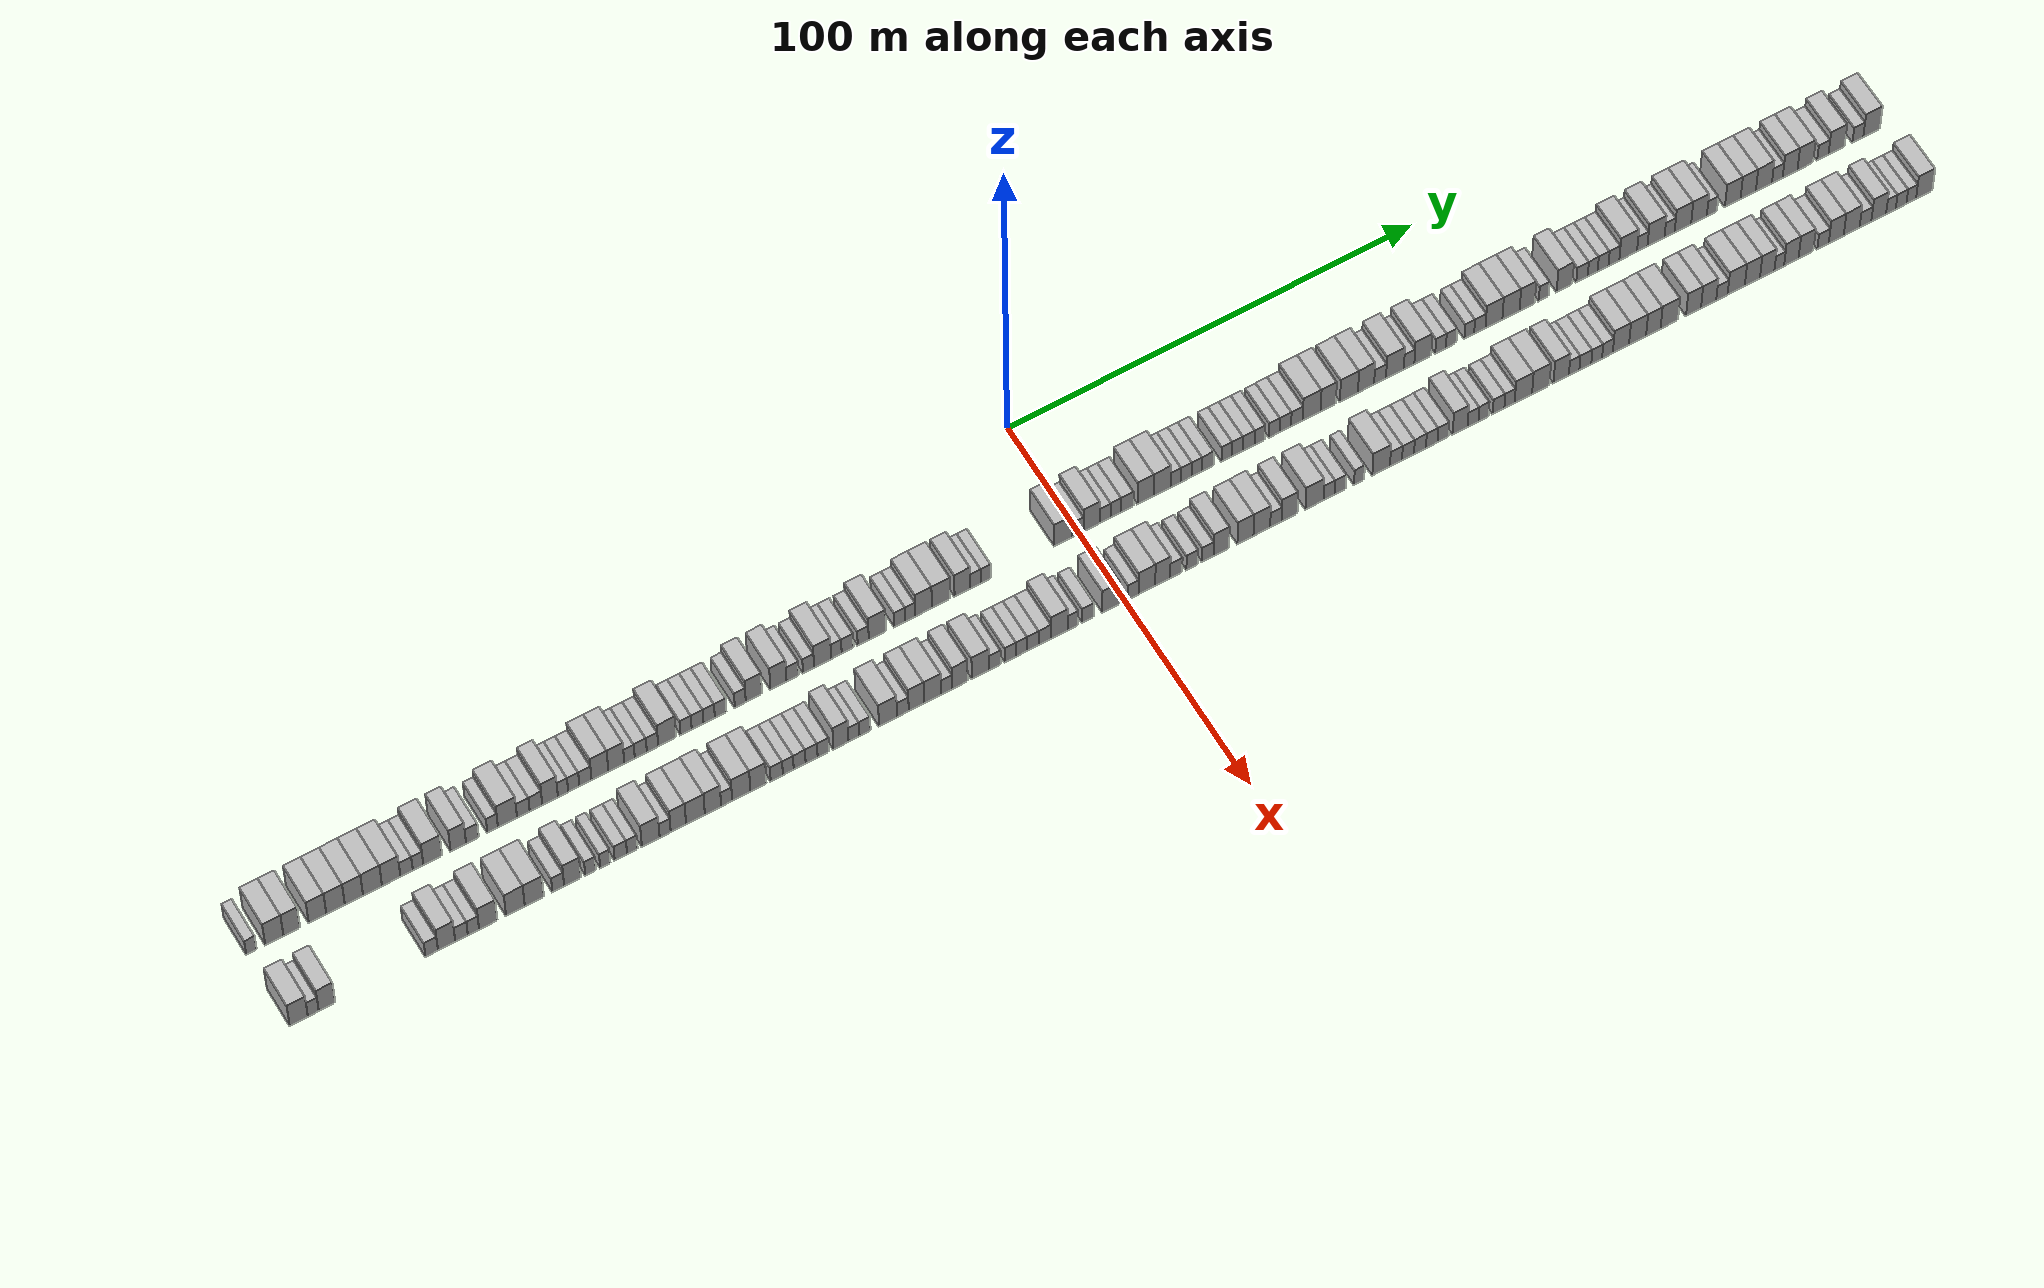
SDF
<sdf version="1.6">
 <world name="default">
  <scene>
   <sky><clouds><speed>12</speed></clouds></sky>
   <ambient>0.4 0.4 0.4 1</ambient>
   <background>0.7 0.7 0.7 1</background>
   <shadows>1</shadows>
  </scene>
  <gravity>0 0 -9.8066</gravity>
  <magnetic_field>6e-06 2.3e-05 -4.2e-05</magnetic_field>
  <physics default="0" name="default_physics" type="ode">
   <ode>
    <solver>
     <type>quick</type>
     <iters>10</iters>
     <sor>1.0</sor>
     <use_dynamic_moi_rescaling>0</use_dynamic_moi_rescaling>
    </solver>
    <constraints>
     <cfm>0</cfm>
     <erp>0.2</erp>
     <contact_max_correcting_vel>100</contact_max_correcting_vel>
     <contact_surface_layer>0.001</contact_surface_layer>
    </constraints>
   </ode>
   <max_step_size>0.004</max_step_size>
   <real_time_factor>1</real_time_factor>
   <real_time_update_rate>250</real_time_update_rate>
  </physics>
  <light name="sun" type="directional">
   <pose>0 0 10 0 0 0</pose>
   <diffuse>0.8 0.8 0.8 1</diffuse>
   <specular>0.2 0.2 0.2 1</specular>
   <attenuation>
    <range>1000</range>
    <constant>0.9</constant>
    <linear>0.01</linear>
    <quadratic>0.001</quadratic>
   </attenuation>
   <direction>-0.5 0.1 -0.9</direction>
  </light>
  <model name="building_1">
   <static>1</static>
   <pose>25.0000 -196.7966 0 0.000000 0.000000 0.000000</pose>
   <link name="link">
    <pose>0 0 3.00 0 0 0</pose>
    <collision name="collision"><geometry><box><size>10.0000 2.4068 6.0000</size></box></geometry></collision>
    <visual name="visual">
     <cast_shadows>0</cast_shadows>
     <geometry><box><size>10.0000 2.4068 6.0000</size></box></geometry>
     <material>
      <script>
       <uri>model://HANNAS_wall/materials/scripts</uri>
       <uri>model://HANNAS_wall/materials/textures</uri>
       <name>vrc/HANNAS_wall</name>
      </script>
     </material>
    </visual>
   </link>
  </model>
  <model name="building_2">
   <static>1</static>
   <pose>25.0000 -191.4744 0 0.000000 0.000000 0.000000</pose>
   <link name="link">
    <pose>0 0 4.50 0 0 0</pose>
    <collision name="collision"><geometry><box><size>10.0000 4.2375 9.0000</size></box></geometry></collision>
    <visual name="visual">
     <cast_shadows>0</cast_shadows>
     <geometry><box><size>10.0000 4.2375 9.0000</size></box></geometry>
     <material>
      <script>
       <uri>model://HANNAS_wall/materials/scripts</uri>
       <uri>model://HANNAS_wall/materials/textures</uri>
       <name>vrc/HANNAS_wall</name>
      </script>
     </material>
    </visual>
   </link>
  </model>
  <model name="building_3">
   <static>1</static>
   <pose>25.0000 -187.4311 0 0.000000 0.000000 0.000000</pose>
   <link name="link">
    <pose>0 0 4.50 0 0 0</pose>
    <collision name="collision"><geometry><box><size>10.0000 3.8492 9.0000</size></box></geometry></collision>
    <visual name="visual">
     <cast_shadows>0</cast_shadows>
     <geometry><box><size>10.0000 3.8492 9.0000</size></box></geometry>
     <material>
      <script>
       <uri>model://HANNAS_wall/materials/scripts</uri>
       <uri>model://HANNAS_wall/materials/textures</uri>
       <name>vrc/HANNAS_wall</name>
      </script>
     </material>
    </visual>
   </link>
  </model>
  <model name="building_4">
   <static>1</static>
   <pose>25.0000 -181.4593 0 0.000000 0.000000 0.000000</pose>
   <link name="link">
    <pose>0 0 4.50 0 0 0</pose>
    <collision name="collision"><geometry><box><size>10.0000 4.0943 9.0000</size></box></geometry></collision>
    <visual name="visual">
     <cast_shadows>0</cast_shadows>
     <geometry><box><size>10.0000 4.0943 9.0000</size></box></geometry>
     <material>
      <script>
       <uri>model://HANNAS_wall/materials/scripts</uri>
       <uri>model://HANNAS_wall/materials/textures</uri>
       <name>vrc/HANNAS_wall</name>
      </script>
     </material>
    </visual>
   </link>
  </model>
  <model name="building_5">
   <static>1</static>
   <pose>25.0000 -177.2593 0 0.000000 0.000000 0.000000</pose>
   <link name="link">
    <pose>0 0 4.50 0 0 0</pose>
    <collision name="collision"><geometry><box><size>10.0000 4.3057 9.0000</size></box></geometry></collision>
    <visual name="visual">
     <cast_shadows>0</cast_shadows>
     <geometry><box><size>10.0000 4.3057 9.0000</size></box></geometry>
     <material>
      <script>
       <uri>model://HANNAS_wall/materials/scripts</uri>
       <uri>model://HANNAS_wall/materials/textures</uri>
       <name>vrc/HANNAS_wall</name>
      </script>
     </material>
    </visual>
   </link>
  </model>
  <model name="building_6">
   <static>1</static>
   <pose>25.0000 -172.9911 0 0.000000 0.000000 0.000000</pose>
   <link name="link">
    <pose>0 0 4.50 0 0 0</pose>
    <collision name="collision"><geometry><box><size>10.0000 4.2307 9.0000</size></box></geometry></collision>
    <visual name="visual">
     <cast_shadows>0</cast_shadows>
     <geometry><box><size>10.0000 4.2307 9.0000</size></box></geometry>
     <material>
      <script>
       <uri>model://HANNAS_wall/materials/scripts</uri>
       <uri>model://HANNAS_wall/materials/textures</uri>
       <name>vrc/HANNAS_wall</name>
      </script>
     </material>
    </visual>
   </link>
  </model>
  <model name="building_7">
   <static>1</static>
   <pose>25.0000 -168.6613 0 0.000000 0.000000 0.000000</pose>
   <link name="link">
    <pose>0 0 4.50 0 0 0</pose>
    <collision name="collision"><geometry><box><size>10.0000 4.4288 9.0000</size></box></geometry></collision>
    <visual name="visual">
     <cast_shadows>0</cast_shadows>
     <geometry><box><size>10.0000 4.4288 9.0000</size></box></geometry>
     <material>
      <script>
       <uri>model://HANNAS_wall/materials/scripts</uri>
       <uri>model://HANNAS_wall/materials/textures</uri>
       <name>vrc/HANNAS_wall</name>
      </script>
     </material>
    </visual>
   </link>
  </model>
  <model name="building_8">
   <static>1</static>
   <pose>25.0000 -164.3003 0 0.000000 0.000000 0.000000</pose>
   <link name="link">
    <pose>0 0 4.50 0 0 0</pose>
    <collision name="collision"><geometry><box><size>10.0000 4.2933 9.0000</size></box></geometry></collision>
    <visual name="visual">
     <cast_shadows>0</cast_shadows>
     <geometry><box><size>10.0000 4.2933 9.0000</size></box></geometry>
     <material>
      <script>
       <uri>model://HANNAS_wall/materials/scripts</uri>
       <uri>model://HANNAS_wall/materials/textures</uri>
       <name>vrc/HANNAS_wall</name>
      </script>
     </material>
    </visual>
   </link>
  </model>
  <model name="building_9">
   <static>1</static>
   <pose>25.0000 -160.7059 0 0.000000 0.000000 0.000000</pose>
   <link name="link">
    <pose>0 0 3.00 0 0 0</pose>
    <collision name="collision"><geometry><box><size>10.0000 2.8955 6.0000</size></box></geometry></collision>
    <visual name="visual">
     <cast_shadows>0</cast_shadows>
     <geometry><box><size>10.0000 2.8955 6.0000</size></box></geometry>
     <material>
      <script>
       <uri>model://HANNAS_wall/materials/scripts</uri>
       <uri>model://HANNAS_wall/materials/textures</uri>
       <name>vrc/HANNAS_wall</name>
      </script>
     </material>
    </visual>
   </link>
  </model>
  <model name="building_10">
   <static>1</static>
   <pose>25.0000 -158.0257 0 0.000000 0.000000 0.000000</pose>
   <link name="link">
    <pose>0 0 3.00 0 0 0</pose>
    <collision name="collision"><geometry><box><size>10.0000 2.4648 6.0000</size></box></geometry></collision>
    <visual name="visual">
     <cast_shadows>0</cast_shadows>
     <geometry><box><size>10.0000 2.4648 6.0000</size></box></geometry>
     <material>
      <script>
       <uri>model://HANNAS_wall/materials/scripts</uri>
       <uri>model://HANNAS_wall/materials/textures</uri>
       <name>vrc/HANNAS_wall</name>
      </script>
     </material>
    </visual>
   </link>
  </model>
  <model name="building_11">
   <static>1</static>
   <pose>25.0000 -154.6019 0 0.000000 0.000000 0.000000</pose>
   <link name="link">
    <pose>0 0 4.50 0 0 0</pose>
    <collision name="collision"><geometry><box><size>10.0000 4.3829 9.0000</size></box></geometry></collision>
    <visual name="visual">
     <cast_shadows>0</cast_shadows>
     <geometry><box><size>10.0000 4.3829 9.0000</size></box></geometry>
     <material>
      <script>
       <uri>model://HANNAS_wall/materials/scripts</uri>
       <uri>model://HANNAS_wall/materials/textures</uri>
       <name>vrc/HANNAS_wall</name>
      </script>
     </material>
    </visual>
   </link>
  </model>
  <model name="building_12">
   <static>1</static>
   <pose>25.0000 -148.5949 0 0.000000 0.000000 0.000000</pose>
   <link name="link">
    <pose>0 0 4.50 0 0 0</pose>
    <collision name="collision"><geometry><box><size>10.0000 3.6311 9.0000</size></box></geometry></collision>
    <visual name="visual">
     <cast_shadows>0</cast_shadows>
     <geometry><box><size>10.0000 3.6311 9.0000</size></box></geometry>
     <material>
      <script>
       <uri>model://HANNAS_wall/materials/scripts</uri>
       <uri>model://HANNAS_wall/materials/textures</uri>
       <name>vrc/HANNAS_wall</name>
      </script>
     </material>
    </visual>
   </link>
  </model>
  <model name="building_13">
   <static>1</static>
   <pose>25.0000 -145.2932 0 0.000000 0.000000 0.000000</pose>
   <link name="link">
    <pose>0 0 3.00 0 0 0</pose>
    <collision name="collision"><geometry><box><size>10.0000 2.9723 6.0000</size></box></geometry></collision>
    <visual name="visual">
     <cast_shadows>0</cast_shadows>
     <geometry><box><size>10.0000 2.9723 6.0000</size></box></geometry>
     <material>
      <script>
       <uri>model://HANNAS_wall/materials/scripts</uri>
       <uri>model://HANNAS_wall/materials/textures</uri>
       <name>vrc/HANNAS_wall</name>
      </script>
     </material>
    </visual>
   </link>
  </model>
  <model name="building_14">
   <static>1</static>
   <pose>25.0000 -140.5572 0 0.000000 0.000000 0.000000</pose>
   <link name="link">
    <pose>0 0 3.00 0 0 0</pose>
    <collision name="collision"><geometry><box><size>10.0000 2.4997 6.0000</size></box></geometry></collision>
    <visual name="visual">
     <cast_shadows>0</cast_shadows>
     <geometry><box><size>10.0000 2.4997 6.0000</size></box></geometry>
     <material>
      <script>
       <uri>model://HANNAS_wall/materials/scripts</uri>
       <uri>model://HANNAS_wall/materials/textures</uri>
       <name>vrc/HANNAS_wall</name>
      </script>
     </material>
    </visual>
   </link>
  </model>
  <model name="building_15">
   <static>1</static>
   <pose>25.0000 -137.0640 0 0.000000 0.000000 0.000000</pose>
   <link name="link">
    <pose>0 0 4.50 0 0 0</pose>
    <collision name="collision"><geometry><box><size>10.0000 4.4868 9.0000</size></box></geometry></collision>
    <visual name="visual">
     <cast_shadows>0</cast_shadows>
     <geometry><box><size>10.0000 4.4868 9.0000</size></box></geometry>
     <material>
      <script>
       <uri>model://HANNAS_wall/materials/scripts</uri>
       <uri>model://HANNAS_wall/materials/textures</uri>
       <name>vrc/HANNAS_wall</name>
      </script>
     </material>
    </visual>
   </link>
  </model>
  <model name="building_16">
   <static>1</static>
   <pose>25.0000 -133.3309 0 0.000000 0.000000 0.000000</pose>
   <link name="link">
    <pose>0 0 3.00 0 0 0</pose>
    <collision name="collision"><geometry><box><size>10.0000 2.9795 6.0000</size></box></geometry></collision>
    <visual name="visual">
     <cast_shadows>0</cast_shadows>
     <geometry><box><size>10.0000 2.9795 6.0000</size></box></geometry>
     <material>
      <script>
       <uri>model://HANNAS_wall/materials/scripts</uri>
       <uri>model://HANNAS_wall/materials/textures</uri>
       <name>vrc/HANNAS_wall</name>
      </script>
     </material>
    </visual>
   </link>
  </model>
  <model name="building_17">
   <static>1</static>
   <pose>25.0000 -130.3622 0 0.000000 0.000000 0.000000</pose>
   <link name="link">
    <pose>0 0 3.00 0 0 0</pose>
    <collision name="collision"><geometry><box><size>10.0000 2.9579 6.0000</size></box></geometry></collision>
    <visual name="visual">
     <cast_shadows>0</cast_shadows>
     <geometry><box><size>10.0000 2.9579 6.0000</size></box></geometry>
     <material>
      <script>
       <uri>model://HANNAS_wall/materials/scripts</uri>
       <uri>model://HANNAS_wall/materials/textures</uri>
       <name>vrc/HANNAS_wall</name>
      </script>
     </material>
    </visual>
   </link>
  </model>
  <model name="building_18">
   <static>1</static>
   <pose>25.0000 -127.0378 0 0.000000 0.000000 0.000000</pose>
   <link name="link">
    <pose>0 0 4.50 0 0 0</pose>
    <collision name="collision"><geometry><box><size>10.0000 3.6909 9.0000</size></box></geometry></collision>
    <visual name="visual">
     <cast_shadows>0</cast_shadows>
     <geometry><box><size>10.0000 3.6909 9.0000</size></box></geometry>
     <material>
      <script>
       <uri>model://HANNAS_wall/materials/scripts</uri>
       <uri>model://HANNAS_wall/materials/textures</uri>
       <name>vrc/HANNAS_wall</name>
      </script>
     </material>
    </visual>
   </link>
  </model>
  <model name="building_19">
   <static>1</static>
   <pose>25.0000 -123.9775 0 0.000000 0.000000 0.000000</pose>
   <link name="link">
    <pose>0 0 3.00 0 0 0</pose>
    <collision name="collision"><geometry><box><size>10.0000 2.4298 6.0000</size></box></geometry></collision>
    <visual name="visual">
     <cast_shadows>0</cast_shadows>
     <geometry><box><size>10.0000 2.4298 6.0000</size></box></geometry>
     <material>
      <script>
       <uri>model://HANNAS_wall/materials/scripts</uri>
       <uri>model://HANNAS_wall/materials/textures</uri>
       <name>vrc/HANNAS_wall</name>
      </script>
     </material>
    </visual>
   </link>
  </model>
  <model name="building_20">
   <static>1</static>
   <pose>25.0000 -121.4424 0 0.000000 0.000000 0.000000</pose>
   <link name="link">
    <pose>0 0 3.00 0 0 0</pose>
    <collision name="collision"><geometry><box><size>10.0000 2.6403 6.0000</size></box></geometry></collision>
    <visual name="visual">
     <cast_shadows>0</cast_shadows>
     <geometry><box><size>10.0000 2.6403 6.0000</size></box></geometry>
     <material>
      <script>
       <uri>model://HANNAS_wall/materials/scripts</uri>
       <uri>model://HANNAS_wall/materials/textures</uri>
       <name>vrc/HANNAS_wall</name>
      </script>
     </material>
    </visual>
   </link>
  </model>
  <model name="building_21">
   <static>1</static>
   <pose>25.0000 -118.6902 0 0.000000 0.000000 0.000000</pose>
   <link name="link">
    <pose>0 0 3.00 0 0 0</pose>
    <collision name="collision"><geometry><box><size>10.0000 2.8641 6.0000</size></box></geometry></collision>
    <visual name="visual">
     <cast_shadows>0</cast_shadows>
     <geometry><box><size>10.0000 2.8641 6.0000</size></box></geometry>
     <material>
      <script>
       <uri>model://HANNAS_wall/materials/scripts</uri>
       <uri>model://HANNAS_wall/materials/textures</uri>
       <name>vrc/HANNAS_wall</name>
      </script>
     </material>
    </visual>
   </link>
  </model>
  <model name="building_22">
   <static>1</static>
   <pose>25.0000 -115.2662 0 0.000000 0.000000 0.000000</pose>
   <link name="link">
    <pose>0 0 4.50 0 0 0</pose>
    <collision name="collision"><geometry><box><size>10.0000 3.9840 9.0000</size></box></geometry></collision>
    <visual name="visual">
     <cast_shadows>0</cast_shadows>
     <geometry><box><size>10.0000 3.9840 9.0000</size></box></geometry>
     <material>
      <script>
       <uri>model://HANNAS_wall/materials/scripts</uri>
       <uri>model://HANNAS_wall/materials/textures</uri>
       <name>vrc/HANNAS_wall</name>
      </script>
     </material>
    </visual>
   </link>
  </model>
  <model name="building_23">
   <static>1</static>
   <pose>25.0000 -111.3850 0 0.000000 0.000000 0.000000</pose>
   <link name="link">
    <pose>0 0 4.50 0 0 0</pose>
    <collision name="collision"><geometry><box><size>10.0000 3.7785 9.0000</size></box></geometry></collision>
    <visual name="visual">
     <cast_shadows>0</cast_shadows>
     <geometry><box><size>10.0000 3.7785 9.0000</size></box></geometry>
     <material>
      <script>
       <uri>model://HANNAS_wall/materials/scripts</uri>
       <uri>model://HANNAS_wall/materials/textures</uri>
       <name>vrc/HANNAS_wall</name>
      </script>
     </material>
    </visual>
   </link>
  </model>
  <model name="building_24">
   <static>1</static>
   <pose>25.0000 -108.2642 0 0.000000 0.000000 0.000000</pose>
   <link name="link">
    <pose>0 0 3.00 0 0 0</pose>
    <collision name="collision"><geometry><box><size>10.0000 2.4630 6.0000</size></box></geometry></collision>
    <visual name="visual">
     <cast_shadows>0</cast_shadows>
     <geometry><box><size>10.0000 2.4630 6.0000</size></box></geometry>
     <material>
      <script>
       <uri>model://HANNAS_wall/materials/scripts</uri>
       <uri>model://HANNAS_wall/materials/textures</uri>
       <name>vrc/HANNAS_wall</name>
      </script>
     </material>
    </visual>
   </link>
  </model>
  <model name="building_25">
   <static>1</static>
   <pose>25.0000 -105.6047 0 0.000000 0.000000 0.000000</pose>
   <link name="link">
    <pose>0 0 3.00 0 0 0</pose>
    <collision name="collision"><geometry><box><size>10.0000 2.8561 6.0000</size></box></geometry></collision>
    <visual name="visual">
     <cast_shadows>0</cast_shadows>
     <geometry><box><size>10.0000 2.8561 6.0000</size></box></geometry>
     <material>
      <script>
       <uri>model://HANNAS_wall/materials/scripts</uri>
       <uri>model://HANNAS_wall/materials/textures</uri>
       <name>vrc/HANNAS_wall</name>
      </script>
     </material>
    </visual>
   </link>
  </model>
  <model name="building_26">
   <static>1</static>
   <pose>25.0000 -102.8159 0 0.000000 0.000000 0.000000</pose>
   <link name="link">
    <pose>0 0 3.00 0 0 0</pose>
    <collision name="collision"><geometry><box><size>10.0000 2.7213 6.0000</size></box></geometry></collision>
    <visual name="visual">
     <cast_shadows>0</cast_shadows>
     <geometry><box><size>10.0000 2.7213 6.0000</size></box></geometry>
     <material>
      <script>
       <uri>model://HANNAS_wall/materials/scripts</uri>
       <uri>model://HANNAS_wall/materials/textures</uri>
       <name>vrc/HANNAS_wall</name>
      </script>
     </material>
    </visual>
   </link>
  </model>
  <model name="building_27">
   <static>1</static>
   <pose>25.0000 -99.3141 0 0.000000 0.000000 0.000000</pose>
   <link name="link">
    <pose>0 0 4.50 0 0 0</pose>
    <collision name="collision"><geometry><box><size>10.0000 4.2824 9.0000</size></box></geometry></collision>
    <visual name="visual">
     <cast_shadows>0</cast_shadows>
     <geometry><box><size>10.0000 4.2824 9.0000</size></box></geometry>
     <material>
      <script>
       <uri>model://HANNAS_wall/materials/scripts</uri>
       <uri>model://HANNAS_wall/materials/textures</uri>
       <name>vrc/HANNAS_wall</name>
      </script>
     </material>
    </visual>
   </link>
  </model>
  <model name="building_28">
   <static>1</static>
   <pose>25.0000 -94.8458 0 0.000000 0.000000 0.000000</pose>
   <link name="link">
    <pose>0 0 3.00 0 0 0</pose>
    <collision name="collision"><geometry><box><size>10.0000 2.6542 6.0000</size></box></geometry></collision>
    <visual name="visual">
     <cast_shadows>0</cast_shadows>
     <geometry><box><size>10.0000 2.6542 6.0000</size></box></geometry>
     <material>
      <script>
       <uri>model://HANNAS_wall/materials/scripts</uri>
       <uri>model://HANNAS_wall/materials/textures</uri>
       <name>vrc/HANNAS_wall</name>
      </script>
     </material>
    </visual>
   </link>
  </model>
  <model name="building_29">
   <static>1</static>
   <pose>25.0000 -92.1096 0 0.000000 0.000000 0.000000</pose>
   <link name="link">
    <pose>0 0 3.00 0 0 0</pose>
    <collision name="collision"><geometry><box><size>10.0000 2.8182 6.0000</size></box></geometry></collision>
    <visual name="visual">
     <cast_shadows>0</cast_shadows>
     <geometry><box><size>10.0000 2.8182 6.0000</size></box></geometry>
     <material>
      <script>
       <uri>model://HANNAS_wall/materials/scripts</uri>
       <uri>model://HANNAS_wall/materials/textures</uri>
       <name>vrc/HANNAS_wall</name>
      </script>
     </material>
    </visual>
   </link>
  </model>
  <model name="building_30">
   <static>1</static>
   <pose>25.0000 -89.3585 0 0.000000 0.000000 0.000000</pose>
   <link name="link">
    <pose>0 0 3.00 0 0 0</pose>
    <collision name="collision"><geometry><box><size>10.0000 2.6840 6.0000</size></box></geometry></collision>
    <visual name="visual">
     <cast_shadows>0</cast_shadows>
     <geometry><box><size>10.0000 2.6840 6.0000</size></box></geometry>
     <material>
      <script>
       <uri>model://HANNAS_wall/materials/scripts</uri>
       <uri>model://HANNAS_wall/materials/textures</uri>
       <name>vrc/HANNAS_wall</name>
      </script>
     </material>
    </visual>
   </link>
  </model>
  <model name="building_31">
   <static>1</static>
   <pose>25.0000 -86.6385 0 0.000000 0.000000 0.000000</pose>
   <link name="link">
    <pose>0 0 3.00 0 0 0</pose>
    <collision name="collision"><geometry><box><size>10.0000 2.7559 6.0000</size></box></geometry></collision>
    <visual name="visual">
     <cast_shadows>0</cast_shadows>
     <geometry><box><size>10.0000 2.7559 6.0000</size></box></geometry>
     <material>
      <script>
       <uri>model://HANNAS_wall/materials/scripts</uri>
       <uri>model://HANNAS_wall/materials/textures</uri>
       <name>vrc/HANNAS_wall</name>
      </script>
     </material>
    </visual>
   </link>
  </model>
  <model name="building_32">
   <static>1</static>
   <pose>25.0000 -81.9549 0 0.000000 0.000000 0.000000</pose>
   <link name="link">
    <pose>0 0 3.00 0 0 0</pose>
    <collision name="collision"><geometry><box><size>10.0000 2.6114 6.0000</size></box></geometry></collision>
    <visual name="visual">
     <cast_shadows>0</cast_shadows>
     <geometry><box><size>10.0000 2.6114 6.0000</size></box></geometry>
     <material>
      <script>
       <uri>model://HANNAS_wall/materials/scripts</uri>
       <uri>model://HANNAS_wall/materials/textures</uri>
       <name>vrc/HANNAS_wall</name>
      </script>
     </material>
    </visual>
   </link>
  </model>
  <model name="building_33">
   <static>1</static>
   <pose>25.0000 -78.7079 0 0.000000 0.000000 0.000000</pose>
   <link name="link">
    <pose>0 0 4.50 0 0 0</pose>
    <collision name="collision"><geometry><box><size>10.0000 3.8826 9.0000</size></box></geometry></collision>
    <visual name="visual">
     <cast_shadows>0</cast_shadows>
     <geometry><box><size>10.0000 3.8826 9.0000</size></box></geometry>
     <material>
      <script>
       <uri>model://HANNAS_wall/materials/scripts</uri>
       <uri>model://HANNAS_wall/materials/textures</uri>
       <name>vrc/HANNAS_wall</name>
      </script>
     </material>
    </visual>
   </link>
  </model>
  <model name="building_34">
   <static>1</static>
   <pose>25.0000 -72.8386 0 0.000000 0.000000 0.000000</pose>
   <link name="link">
    <pose>0 0 4.50 0 0 0</pose>
    <collision name="collision"><geometry><box><size>10.0000 3.8561 9.0000</size></box></geometry></collision>
    <visual name="visual">
     <cast_shadows>0</cast_shadows>
     <geometry><box><size>10.0000 3.8561 9.0000</size></box></geometry>
     <material>
      <script>
       <uri>model://HANNAS_wall/materials/scripts</uri>
       <uri>model://HANNAS_wall/materials/textures</uri>
       <name>vrc/HANNAS_wall</name>
      </script>
     </material>
    </visual>
   </link>
  </model>
  <model name="building_35">
   <static>1</static>
   <pose>25.0000 -69.4504 0 0.000000 0.000000 0.000000</pose>
   <link name="link">
    <pose>0 0 3.00 0 0 0</pose>
    <collision name="collision"><geometry><box><size>10.0000 2.9203 6.0000</size></box></geometry></collision>
    <visual name="visual">
     <cast_shadows>0</cast_shadows>
     <geometry><box><size>10.0000 2.9203 6.0000</size></box></geometry>
     <material>
      <script>
       <uri>model://HANNAS_wall/materials/scripts</uri>
       <uri>model://HANNAS_wall/materials/textures</uri>
       <name>vrc/HANNAS_wall</name>
      </script>
     </material>
    </visual>
   </link>
  </model>
  <model name="building_36">
   <static>1</static>
   <pose>25.0000 -65.6595 0 0.000000 0.000000 0.000000</pose>
   <link name="link">
    <pose>0 0 3.00 0 0 0</pose>
    <collision name="collision"><geometry><box><size>10.0000 2.6615 6.0000</size></box></geometry></collision>
    <visual name="visual">
     <cast_shadows>0</cast_shadows>
     <geometry><box><size>10.0000 2.6615 6.0000</size></box></geometry>
     <material>
      <script>
       <uri>model://HANNAS_wall/materials/scripts</uri>
       <uri>model://HANNAS_wall/materials/textures</uri>
       <name>vrc/HANNAS_wall</name>
      </script>
     </material>
    </visual>
   </link>
  </model>
  <model name="building_37">
   <static>1</static>
   <pose>25.0000 -62.2819 0 0.000000 0.000000 0.000000</pose>
   <link name="link">
    <pose>0 0 4.50 0 0 0</pose>
    <collision name="collision"><geometry><box><size>10.0000 4.0937 9.0000</size></box></geometry></collision>
    <visual name="visual">
     <cast_shadows>0</cast_shadows>
     <geometry><box><size>10.0000 4.0937 9.0000</size></box></geometry>
     <material>
      <script>
       <uri>model://HANNAS_wall/materials/scripts</uri>
       <uri>model://HANNAS_wall/materials/textures</uri>
       <name>vrc/HANNAS_wall</name>
      </script>
     </material>
    </visual>
   </link>
  </model>
  <model name="building_38">
   <static>1</static>
   <pose>25.0000 -58.9693 0 0.000000 0.000000 0.000000</pose>
   <link name="link">
    <pose>0 0 3.00 0 0 0</pose>
    <collision name="collision"><geometry><box><size>10.0000 2.5316 6.0000</size></box></geometry></collision>
    <visual name="visual">
     <cast_shadows>0</cast_shadows>
     <geometry><box><size>10.0000 2.5316 6.0000</size></box></geometry>
     <material>
      <script>
       <uri>model://HANNAS_wall/materials/scripts</uri>
       <uri>model://HANNAS_wall/materials/textures</uri>
       <name>vrc/HANNAS_wall</name>
      </script>
     </material>
    </visual>
   </link>
  </model>
  <model name="building_39">
   <static>1</static>
   <pose>25.0000 -56.2796 0 0.000000 0.000000 0.000000</pose>
   <link name="link">
    <pose>0 0 3.00 0 0 0</pose>
    <collision name="collision"><geometry><box><size>10.0000 2.8477 6.0000</size></box></geometry></collision>
    <visual name="visual">
     <cast_shadows>0</cast_shadows>
     <geometry><box><size>10.0000 2.8477 6.0000</size></box></geometry>
     <material>
      <script>
       <uri>model://HANNAS_wall/materials/scripts</uri>
       <uri>model://HANNAS_wall/materials/textures</uri>
       <name>vrc/HANNAS_wall</name>
      </script>
     </material>
    </visual>
   </link>
  </model>
  <model name="building_40">
   <static>1</static>
   <pose>25.0000 -52.5273 0 0.000000 0.000000 0.000000</pose>
   <link name="link">
    <pose>0 0 3.00 0 0 0</pose>
    <collision name="collision"><geometry><box><size>10.0000 2.6569 6.0000</size></box></geometry></collision>
    <visual name="visual">
     <cast_shadows>0</cast_shadows>
     <geometry><box><size>10.0000 2.6569 6.0000</size></box></geometry>
     <material>
      <script>
       <uri>model://HANNAS_wall/materials/scripts</uri>
       <uri>model://HANNAS_wall/materials/textures</uri>
       <name>vrc/HANNAS_wall</name>
      </script>
     </material>
    </visual>
   </link>
  </model>
  <model name="building_41">
   <static>1</static>
   <pose>25.0000 -49.1151 0 0.000000 0.000000 0.000000</pose>
   <link name="link">
    <pose>0 0 4.50 0 0 0</pose>
    <collision name="collision"><geometry><box><size>10.0000 4.1675 9.0000</size></box></geometry></collision>
    <visual name="visual">
     <cast_shadows>0</cast_shadows>
     <geometry><box><size>10.0000 4.1675 9.0000</size></box></geometry>
     <material>
      <script>
       <uri>model://HANNAS_wall/materials/scripts</uri>
       <uri>model://HANNAS_wall/materials/textures</uri>
       <name>vrc/HANNAS_wall</name>
      </script>
     </material>
    </visual>
   </link>
  </model>
  <model name="building_42">
   <static>1</static>
   <pose>25.0000 -43.7156 0 0.000000 0.000000 0.000000</pose>
   <link name="link">
    <pose>0 0 3.00 0 0 0</pose>
    <collision name="collision"><geometry><box><size>10.0000 2.6314 6.0000</size></box></geometry></collision>
    <visual name="visual">
     <cast_shadows>0</cast_shadows>
     <geometry><box><size>10.0000 2.6314 6.0000</size></box></geometry>
     <material>
      <script>
       <uri>model://HANNAS_wall/materials/scripts</uri>
       <uri>model://HANNAS_wall/materials/textures</uri>
       <name>vrc/HANNAS_wall</name>
      </script>
     </material>
    </visual>
   </link>
  </model>
  <model name="building_43">
   <static>1</static>
   <pose>25.0000 -41.1947 0 0.000000 0.000000 0.000000</pose>
   <link name="link">
    <pose>0 0 3.00 0 0 0</pose>
    <collision name="collision"><geometry><box><size>10.0000 2.4105 6.0000</size></box></geometry></collision>
    <visual name="visual">
     <cast_shadows>0</cast_shadows>
     <geometry><box><size>10.0000 2.4105 6.0000</size></box></geometry>
     <material>
      <script>
       <uri>model://HANNAS_wall/materials/scripts</uri>
       <uri>model://HANNAS_wall/materials/textures</uri>
       <name>vrc/HANNAS_wall</name>
      </script>
     </material>
    </visual>
   </link>
  </model>
  <model name="building_44">
   <static>1</static>
   <pose>25.0000 -37.9845 0 0.000000 0.000000 0.000000</pose>
   <link name="link">
    <pose>0 0 4.50 0 0 0</pose>
    <collision name="collision"><geometry><box><size>10.0000 4.0098 9.0000</size></box></geometry></collision>
    <visual name="visual">
     <cast_shadows>0</cast_shadows>
     <geometry><box><size>10.0000 4.0098 9.0000</size></box></geometry>
     <material>
      <script>
       <uri>model://HANNAS_wall/materials/scripts</uri>
       <uri>model://HANNAS_wall/materials/textures</uri>
       <name>vrc/HANNAS_wall</name>
      </script>
     </material>
    </visual>
   </link>
  </model>
  <model name="building_45">
   <static>1</static>
   <pose>25.0000 -33.7493 0 0.000000 0.000000 0.000000</pose>
   <link name="link">
    <pose>0 0 4.50 0 0 0</pose>
    <collision name="collision"><geometry><box><size>10.0000 4.4606 9.0000</size></box></geometry></collision>
    <visual name="visual">
     <cast_shadows>0</cast_shadows>
     <geometry><box><size>10.0000 4.4606 9.0000</size></box></geometry>
     <material>
      <script>
       <uri>model://HANNAS_wall/materials/scripts</uri>
       <uri>model://HANNAS_wall/materials/textures</uri>
       <name>vrc/HANNAS_wall</name>
      </script>
     </material>
    </visual>
   </link>
  </model>
  <model name="building_46">
   <static>1</static>
   <pose>25.0000 -28.6179 0 0.000000 0.000000 0.000000</pose>
   <link name="link">
    <pose>0 0 4.50 0 0 0</pose>
    <collision name="collision"><geometry><box><size>10.0000 3.8022 9.0000</size></box></geometry></collision>
    <visual name="visual">
     <cast_shadows>0</cast_shadows>
     <geometry><box><size>10.0000 3.8022 9.0000</size></box></geometry>
     <material>
      <script>
       <uri>model://HANNAS_wall/materials/scripts</uri>
       <uri>model://HANNAS_wall/materials/textures</uri>
       <name>vrc/HANNAS_wall</name>
      </script>
     </material>
    </visual>
   </link>
  </model>
  <model name="building_47">
   <static>1</static>
   <pose>25.0000 -25.4377 0 0.000000 0.000000 0.000000</pose>
   <link name="link">
    <pose>0 0 3.00 0 0 0</pose>
    <collision name="collision"><geometry><box><size>10.0000 2.5583 6.0000</size></box></geometry></collision>
    <visual name="visual">
     <cast_shadows>0</cast_shadows>
     <geometry><box><size>10.0000 2.5583 6.0000</size></box></geometry>
     <material>
      <script>
       <uri>model://HANNAS_wall/materials/scripts</uri>
       <uri>model://HANNAS_wall/materials/textures</uri>
       <name>vrc/HANNAS_wall</name>
      </script>
     </material>
    </visual>
   </link>
  </model>
  <model name="building_48">
   <static>1</static>
   <pose>25.0000 -22.9423 0 0.000000 0.000000 0.000000</pose>
   <link name="link">
    <pose>0 0 3.00 0 0 0</pose>
    <collision name="collision"><geometry><box><size>10.0000 2.4326 6.0000</size></box></geometry></collision>
    <visual name="visual">
     <cast_shadows>0</cast_shadows>
     <geometry><box><size>10.0000 2.4326 6.0000</size></box></geometry>
     <material>
      <script>
       <uri>model://HANNAS_wall/materials/scripts</uri>
       <uri>model://HANNAS_wall/materials/textures</uri>
       <name>vrc/HANNAS_wall</name>
      </script>
     </material>
    </visual>
   </link>
  </model>
  <model name="building_49">
   <static>1</static>
   <pose>25.0000 -4.1322 0 0.000000 0.000000 0.000000</pose>
   <link name="link">
    <pose>0 0 4.50 0 0 0</pose>
    <collision name="collision"><geometry><box><size>10.0000 4.3958 9.0000</size></box></geometry></collision>
    <visual name="visual">
     <cast_shadows>0</cast_shadows>
     <geometry><box><size>10.0000 4.3958 9.0000</size></box></geometry>
     <material>
      <script>
       <uri>model://HANNAS_wall/materials/scripts</uri>
       <uri>model://HANNAS_wall/materials/textures</uri>
       <name>vrc/HANNAS_wall</name>
      </script>
     </material>
    </visual>
   </link>
  </model>
  <model name="building_50">
   <static>1</static>
   <pose>25.0000 -0.5826 0 0.000000 0.000000 0.000000</pose>
   <link name="link">
    <pose>0 0 3.00 0 0 0</pose>
    <collision name="collision"><geometry><box><size>10.0000 2.7035 6.0000</size></box></geometry></collision>
    <visual name="visual">
     <cast_shadows>0</cast_shadows>
     <geometry><box><size>10.0000 2.7035 6.0000</size></box></geometry>
     <material>
      <script>
       <uri>model://HANNAS_wall/materials/scripts</uri>
       <uri>model://HANNAS_wall/materials/textures</uri>
       <name>vrc/HANNAS_wall</name>
      </script>
     </material>
    </visual>
   </link>
  </model>
  <model name="building_51">
   <static>1</static>
   <pose>25.0000 2.7589 0 0.000000 0.000000 0.000000</pose>
   <link name="link">
    <pose>0 0 4.50 0 0 0</pose>
    <collision name="collision"><geometry><box><size>10.0000 3.9795 9.0000</size></box></geometry></collision>
    <visual name="visual">
     <cast_shadows>0</cast_shadows>
     <geometry><box><size>10.0000 3.9795 9.0000</size></box></geometry>
     <material>
      <script>
       <uri>model://HANNAS_wall/materials/scripts</uri>
       <uri>model://HANNAS_wall/materials/textures</uri>
       <name>vrc/HANNAS_wall</name>
      </script>
     </material>
    </visual>
   </link>
  </model>
  <model name="building_52">
   <static>1</static>
   <pose>25.0000 6.0873 0 0.000000 0.000000 0.000000</pose>
   <link name="link">
    <pose>0 0 3.00 0 0 0</pose>
    <collision name="collision"><geometry><box><size>10.0000 2.6772 6.0000</size></box></geometry></collision>
    <visual name="visual">
     <cast_shadows>0</cast_shadows>
     <geometry><box><size>10.0000 2.6772 6.0000</size></box></geometry>
     <material>
      <script>
       <uri>model://HANNAS_wall/materials/scripts</uri>
       <uri>model://HANNAS_wall/materials/textures</uri>
       <name>vrc/HANNAS_wall</name>
      </script>
     </material>
    </visual>
   </link>
  </model>
  <model name="building_53">
   <static>1</static>
   <pose>25.0000 8.7115 0 0.000000 0.000000 0.000000</pose>
   <link name="link">
    <pose>0 0 3.00 0 0 0</pose>
    <collision name="collision"><geometry><box><size>10.0000 2.5713 6.0000</size></box></geometry></collision>
    <visual name="visual">
     <cast_shadows>0</cast_shadows>
     <geometry><box><size>10.0000 2.5713 6.0000</size></box></geometry>
     <material>
      <script>
       <uri>model://HANNAS_wall/materials/scripts</uri>
       <uri>model://HANNAS_wall/materials/textures</uri>
       <name>vrc/HANNAS_wall</name>
      </script>
     </material>
    </visual>
   </link>
  </model>
  <model name="building_54">
   <static>1</static>
   <pose>25.0000 11.4802 0 0.000000 0.000000 0.000000</pose>
   <link name="link">
    <pose>0 0 3.00 0 0 0</pose>
    <collision name="collision"><geometry><box><size>10.0000 2.9660 6.0000</size></box></geometry></collision>
    <visual name="visual">
     <cast_shadows>0</cast_shadows>
     <geometry><box><size>10.0000 2.9660 6.0000</size></box></geometry>
     <material>
      <script>
       <uri>model://HANNAS_wall/materials/scripts</uri>
       <uri>model://HANNAS_wall/materials/textures</uri>
       <name>vrc/HANNAS_wall</name>
      </script>
     </material>
    </visual>
   </link>
  </model>
  <model name="building_55">
   <static>1</static>
   <pose>25.0000 15.9163 0 0.000000 0.000000 0.000000</pose>
   <link name="link">
    <pose>0 0 4.50 0 0 0</pose>
    <collision name="collision"><geometry><box><size>10.0000 3.9062 9.0000</size></box></geometry></collision>
    <visual name="visual">
     <cast_shadows>0</cast_shadows>
     <geometry><box><size>10.0000 3.9062 9.0000</size></box></geometry>
     <material>
      <script>
       <uri>model://HANNAS_wall/materials/scripts</uri>
       <uri>model://HANNAS_wall/materials/textures</uri>
       <name>vrc/HANNAS_wall</name>
      </script>
     </material>
    </visual>
   </link>
  </model>
  <model name="building_56">
   <static>1</static>
   <pose>25.0000 19.9657 0 0.000000 0.000000 0.000000</pose>
   <link name="link">
    <pose>0 0 4.50 0 0 0</pose>
    <collision name="collision"><geometry><box><size>10.0000 4.1926 9.0000</size></box></geometry></collision>
    <visual name="visual">
     <cast_shadows>0</cast_shadows>
     <geometry><box><size>10.0000 4.1926 9.0000</size></box></geometry>
     <material>
      <script>
       <uri>model://HANNAS_wall/materials/scripts</uri>
       <uri>model://HANNAS_wall/materials/textures</uri>
       <name>vrc/HANNAS_wall</name>
      </script>
     </material>
    </visual>
   </link>
  </model>
  <model name="building_57">
   <static>1</static>
   <pose>25.0000 23.3356 0 0.000000 0.000000 0.000000</pose>
   <link name="link">
    <pose>0 0 3.00 0 0 0</pose>
    <collision name="collision"><geometry><box><size>10.0000 2.5472 6.0000</size></box></geometry></collision>
    <visual name="visual">
     <cast_shadows>0</cast_shadows>
     <geometry><box><size>10.0000 2.5472 6.0000</size></box></geometry>
     <material>
      <script>
       <uri>model://HANNAS_wall/materials/scripts</uri>
       <uri>model://HANNAS_wall/materials/textures</uri>
       <name>vrc/HANNAS_wall</name>
      </script>
     </material>
    </visual>
   </link>
  </model>
  <model name="building_58">
   <static>1</static>
   <pose>25.0000 25.9146 0 0.000000 0.000000 0.000000</pose>
   <link name="link">
    <pose>0 0 3.00 0 0 0</pose>
    <collision name="collision"><geometry><box><size>10.0000 2.6108 6.0000</size></box></geometry></collision>
    <visual name="visual">
     <cast_shadows>0</cast_shadows>
     <geometry><box><size>10.0000 2.6108 6.0000</size></box></geometry>
     <material>
      <script>
       <uri>model://HANNAS_wall/materials/scripts</uri>
       <uri>model://HANNAS_wall/materials/textures</uri>
       <name>vrc/HANNAS_wall</name>
      </script>
     </material>
    </visual>
   </link>
  </model>
  <model name="building_59">
   <static>1</static>
   <pose>25.0000 28.4655 0 0.000000 0.000000 0.000000</pose>
   <link name="link">
    <pose>0 0 3.00 0 0 0</pose>
    <collision name="collision"><geometry><box><size>10.0000 2.4911 6.0000</size></box></geometry></collision>
    <visual name="visual">
     <cast_shadows>0</cast_shadows>
     <geometry><box><size>10.0000 2.4911 6.0000</size></box></geometry>
     <material>
      <script>
       <uri>model://HANNAS_wall/materials/scripts</uri>
       <uri>model://HANNAS_wall/materials/textures</uri>
       <name>vrc/HANNAS_wall</name>
      </script>
     </material>
    </visual>
   </link>
  </model>
  <model name="building_60">
   <static>1</static>
   <pose>25.0000 31.1306 0 0.000000 0.000000 0.000000</pose>
   <link name="link">
    <pose>0 0 3.00 0 0 0</pose>
    <collision name="collision"><geometry><box><size>10.0000 2.8390 6.0000</size></box></geometry></collision>
    <visual name="visual">
     <cast_shadows>0</cast_shadows>
     <geometry><box><size>10.0000 2.8390 6.0000</size></box></geometry>
     <material>
      <script>
       <uri>model://HANNAS_wall/materials/scripts</uri>
       <uri>model://HANNAS_wall/materials/textures</uri>
       <name>vrc/HANNAS_wall</name>
      </script>
     </material>
    </visual>
   </link>
  </model>
  <model name="building_61">
   <static>1</static>
   <pose>25.0000 35.8308 0 0.000000 0.000000 0.000000</pose>
   <link name="link">
    <pose>0 0 3.00 0 0 0</pose>
    <collision name="collision"><geometry><box><size>10.0000 2.5614 6.0000</size></box></geometry></collision>
    <visual name="visual">
     <cast_shadows>0</cast_shadows>
     <geometry><box><size>10.0000 2.5614 6.0000</size></box></geometry>
     <material>
      <script>
       <uri>model://HANNAS_wall/materials/scripts</uri>
       <uri>model://HANNAS_wall/materials/textures</uri>
       <name>vrc/HANNAS_wall</name>
      </script>
     </material>
    </visual>
   </link>
  </model>
  <model name="building_62">
   <static>1</static>
   <pose>25.0000 38.4246 0 0.000000 0.000000 0.000000</pose>
   <link name="link">
    <pose>0 0 3.00 0 0 0</pose>
    <collision name="collision"><geometry><box><size>10.0000 2.6260 6.0000</size></box></geometry></collision>
    <visual name="visual">
     <cast_shadows>0</cast_shadows>
     <geometry><box><size>10.0000 2.6260 6.0000</size></box></geometry>
     <material>
      <script>
       <uri>model://HANNAS_wall/materials/scripts</uri>
       <uri>model://HANNAS_wall/materials/textures</uri>
       <name>vrc/HANNAS_wall</name>
      </script>
     </material>
    </visual>
   </link>
  </model>
  <model name="building_63">
   <static>1</static>
   <pose>25.0000 41.2061 0 0.000000 0.000000 0.000000</pose>
   <link name="link">
    <pose>0 0 3.00 0 0 0</pose>
    <collision name="collision"><geometry><box><size>10.0000 2.9372 6.0000</size></box></geometry></collision>
    <visual name="visual">
     <cast_shadows>0</cast_shadows>
     <geometry><box><size>10.0000 2.9372 6.0000</size></box></geometry>
     <material>
      <script>
       <uri>model://HANNAS_wall/materials/scripts</uri>
       <uri>model://HANNAS_wall/materials/textures</uri>
       <name>vrc/HANNAS_wall</name>
      </script>
     </material>
    </visual>
   </link>
  </model>
  <model name="building_64">
   <static>1</static>
   <pose>25.0000 43.9478 0 0.000000 0.000000 0.000000</pose>
   <link name="link">
    <pose>0 0 3.00 0 0 0</pose>
    <collision name="collision"><geometry><box><size>10.0000 2.5462 6.0000</size></box></geometry></collision>
    <visual name="visual">
     <cast_shadows>0</cast_shadows>
     <geometry><box><size>10.0000 2.5462 6.0000</size></box></geometry>
     <material>
      <script>
       <uri>model://HANNAS_wall/materials/scripts</uri>
       <uri>model://HANNAS_wall/materials/textures</uri>
       <name>vrc/HANNAS_wall</name>
      </script>
     </material>
    </visual>
   </link>
  </model>
  <model name="building_65">
   <static>1</static>
   <pose>25.0000 47.5077 0 0.000000 0.000000 0.000000</pose>
   <link name="link">
    <pose>0 0 3.00 0 0 0</pose>
    <collision name="collision"><geometry><box><size>10.0000 2.5735 6.0000</size></box></geometry></collision>
    <visual name="visual">
     <cast_shadows>0</cast_shadows>
     <geometry><box><size>10.0000 2.5735 6.0000</size></box></geometry>
     <material>
      <script>
       <uri>model://HANNAS_wall/materials/scripts</uri>
       <uri>model://HANNAS_wall/materials/textures</uri>
       <name>vrc/HANNAS_wall</name>
      </script>
     </material>
    </visual>
   </link>
  </model>
  <model name="building_66">
   <static>1</static>
   <pose>25.0000 50.2321 0 0.000000 0.000000 0.000000</pose>
   <link name="link">
    <pose>0 0 3.00 0 0 0</pose>
    <collision name="collision"><geometry><box><size>10.0000 2.8752 6.0000</size></box></geometry></collision>
    <visual name="visual">
     <cast_shadows>0</cast_shadows>
     <geometry><box><size>10.0000 2.8752 6.0000</size></box></geometry>
     <material>
      <script>
       <uri>model://HANNAS_wall/materials/scripts</uri>
       <uri>model://HANNAS_wall/materials/textures</uri>
       <name>vrc/HANNAS_wall</name>
      </script>
     </material>
    </visual>
   </link>
  </model>
  <model name="building_67">
   <static>1</static>
   <pose>25.0000 53.1093 0 0.000000 0.000000 0.000000</pose>
   <link name="link">
    <pose>0 0 3.00 0 0 0</pose>
    <collision name="collision"><geometry><box><size>10.0000 2.8793 6.0000</size></box></geometry></collision>
    <visual name="visual">
     <cast_shadows>0</cast_shadows>
     <geometry><box><size>10.0000 2.8793 6.0000</size></box></geometry>
     <material>
      <script>
       <uri>model://HANNAS_wall/materials/scripts</uri>
       <uri>model://HANNAS_wall/materials/textures</uri>
       <name>vrc/HANNAS_wall</name>
      </script>
     </material>
    </visual>
   </link>
  </model>
  <model name="building_68">
   <static>1</static>
   <pose>25.0000 56.7665 0 0.000000 0.000000 0.000000</pose>
   <link name="link">
    <pose>0 0 4.50 0 0 0</pose>
    <collision name="collision"><geometry><box><size>10.0000 4.4350 9.0000</size></box></geometry></collision>
    <visual name="visual">
     <cast_shadows>0</cast_shadows>
     <geometry><box><size>10.0000 4.4350 9.0000</size></box></geometry>
     <material>
      <script>
       <uri>model://HANNAS_wall/materials/scripts</uri>
       <uri>model://HANNAS_wall/materials/textures</uri>
       <name>vrc/HANNAS_wall</name>
      </script>
     </material>
    </visual>
   </link>
  </model>
  <model name="building_69">
   <static>1</static>
   <pose>25.0000 60.8629 0 0.000000 0.000000 0.000000</pose>
   <link name="link">
    <pose>0 0 4.50 0 0 0</pose>
    <collision name="collision"><geometry><box><size>10.0000 3.7578 9.0000</size></box></geometry></collision>
    <visual name="visual">
     <cast_shadows>0</cast_shadows>
     <geometry><box><size>10.0000 3.7578 9.0000</size></box></geometry>
     <material>
      <script>
       <uri>model://HANNAS_wall/materials/scripts</uri>
       <uri>model://HANNAS_wall/materials/textures</uri>
       <name>vrc/HANNAS_wall</name>
      </script>
     </material>
    </visual>
   </link>
  </model>
  <model name="building_70">
   <static>1</static>
   <pose>25.0000 65.9792 0 0.000000 0.000000 0.000000</pose>
   <link name="link">
    <pose>0 0 4.50 0 0 0</pose>
    <collision name="collision"><geometry><box><size>10.0000 4.4748 9.0000</size></box></geometry></collision>
    <visual name="visual">
     <cast_shadows>0</cast_shadows>
     <geometry><box><size>10.0000 4.4748 9.0000</size></box></geometry>
     <material>
      <script>
       <uri>model://HANNAS_wall/materials/scripts</uri>
       <uri>model://HANNAS_wall/materials/textures</uri>
       <name>vrc/HANNAS_wall</name>
      </script>
     </material>
    </visual>
   </link>
  </model>
  <model name="building_71">
   <static>1</static>
   <pose>25.0000 70.2125 0 0.000000 0.000000 0.000000</pose>
   <link name="link">
    <pose>0 0 4.50 0 0 0</pose>
    <collision name="collision"><geometry><box><size>10.0000 3.9920 9.0000</size></box></geometry></collision>
    <visual name="visual">
     <cast_shadows>0</cast_shadows>
     <geometry><box><size>10.0000 3.9920 9.0000</size></box></geometry>
     <material>
      <script>
       <uri>model://HANNAS_wall/materials/scripts</uri>
       <uri>model://HANNAS_wall/materials/textures</uri>
       <name>vrc/HANNAS_wall</name>
      </script>
     </material>
    </visual>
   </link>
  </model>
  <model name="building_72">
   <static>1</static>
   <pose>25.0000 73.6860 0 0.000000 0.000000 0.000000</pose>
   <link name="link">
    <pose>0 0 3.00 0 0 0</pose>
    <collision name="collision"><geometry><box><size>10.0000 2.9551 6.0000</size></box></geometry></collision>
    <visual name="visual">
     <cast_shadows>0</cast_shadows>
     <geometry><box><size>10.0000 2.9551 6.0000</size></box></geometry>
     <material>
      <script>
       <uri>model://HANNAS_wall/materials/scripts</uri>
       <uri>model://HANNAS_wall/materials/textures</uri>
       <name>vrc/HANNAS_wall</name>
      </script>
     </material>
    </visual>
   </link>
  </model>
  <model name="building_73">
   <static>1</static>
   <pose>25.0000 77.3715 0 0.000000 0.000000 0.000000</pose>
   <link name="link">
    <pose>0 0 4.50 0 0 0</pose>
    <collision name="collision"><geometry><box><size>10.0000 4.4159 9.0000</size></box></geometry></collision>
    <visual name="visual">
     <cast_shadows>0</cast_shadows>
     <geometry><box><size>10.0000 4.4159 9.0000</size></box></geometry>
     <material>
      <script>
       <uri>model://HANNAS_wall/materials/scripts</uri>
       <uri>model://HANNAS_wall/materials/textures</uri>
       <name>vrc/HANNAS_wall</name>
      </script>
     </material>
    </visual>
   </link>
  </model>
  <model name="building_74">
   <static>1</static>
   <pose>25.0000 80.8892 0 0.000000 0.000000 0.000000</pose>
   <link name="link">
    <pose>0 0 3.00 0 0 0</pose>
    <collision name="collision"><geometry><box><size>10.0000 2.6195 6.0000</size></box></geometry></collision>
    <visual name="visual">
     <cast_shadows>0</cast_shadows>
     <geometry><box><size>10.0000 2.6195 6.0000</size></box></geometry>
     <material>
      <script>
       <uri>model://HANNAS_wall/materials/scripts</uri>
       <uri>model://HANNAS_wall/materials/textures</uri>
       <name>vrc/HANNAS_wall</name>
      </script>
     </material>
    </visual>
   </link>
  </model>
  <model name="building_75">
   <static>1</static>
   <pose>25.0000 84.2985 0 0.000000 0.000000 0.000000</pose>
   <link name="link">
    <pose>0 0 4.50 0 0 0</pose>
    <collision name="collision"><geometry><box><size>10.0000 4.1991 9.0000</size></box></geometry></collision>
    <visual name="visual">
     <cast_shadows>0</cast_shadows>
     <geometry><box><size>10.0000 4.1991 9.0000</size></box></geometry>
     <material>
      <script>
       <uri>model://HANNAS_wall/materials/scripts</uri>
       <uri>model://HANNAS_wall/materials/textures</uri>
       <name>vrc/HANNAS_wall</name>
      </script>
     </material>
    </visual>
   </link>
  </model>
  <model name="building_76">
   <static>1</static>
   <pose>25.0000 88.7278 0 0.000000 0.000000 0.000000</pose>
   <link name="link">
    <pose>0 0 3.00 0 0 0</pose>
    <collision name="collision"><geometry><box><size>10.0000 2.6595 6.0000</size></box></geometry></collision>
    <visual name="visual">
     <cast_shadows>0</cast_shadows>
     <geometry><box><size>10.0000 2.6595 6.0000</size></box></geometry>
     <material>
      <script>
       <uri>model://HANNAS_wall/materials/scripts</uri>
       <uri>model://HANNAS_wall/materials/textures</uri>
       <name>vrc/HANNAS_wall</name>
      </script>
     </material>
    </visual>
   </link>
  </model>
  <model name="building_77">
   <static>1</static>
   <pose>25.0000 91.3631 0 0.000000 0.000000 0.000000</pose>
   <link name="link">
    <pose>0 0 3.00 0 0 0</pose>
    <collision name="collision"><geometry><box><size>10.0000 2.6112 6.0000</size></box></geometry></collision>
    <visual name="visual">
     <cast_shadows>0</cast_shadows>
     <geometry><box><size>10.0000 2.6112 6.0000</size></box></geometry>
     <material>
      <script>
       <uri>model://HANNAS_wall/materials/scripts</uri>
       <uri>model://HANNAS_wall/materials/textures</uri>
       <name>vrc/HANNAS_wall</name>
      </script>
     </material>
    </visual>
   </link>
  </model>
  <model name="building_78">
   <static>1</static>
   <pose>25.0000 95.8824 0 0.000000 0.000000 0.000000</pose>
   <link name="link">
    <pose>0 0 3.00 0 0 0</pose>
    <collision name="collision"><geometry><box><size>10.0000 2.4275 6.0000</size></box></geometry></collision>
    <visual name="visual">
     <cast_shadows>0</cast_shadows>
     <geometry><box><size>10.0000 2.4275 6.0000</size></box></geometry>
     <material>
      <script>
       <uri>model://HANNAS_wall/materials/scripts</uri>
       <uri>model://HANNAS_wall/materials/textures</uri>
       <name>vrc/HANNAS_wall</name>
      </script>
     </material>
    </visual>
   </link>
  </model>
  <model name="building_79">
   <static>1</static>
   <pose>25.0000 98.5160 0 0.000000 0.000000 0.000000</pose>
   <link name="link">
    <pose>0 0 3.00 0 0 0</pose>
    <collision name="collision"><geometry><box><size>10.0000 2.8397 6.0000</size></box></geometry></collision>
    <visual name="visual">
     <cast_shadows>0</cast_shadows>
     <geometry><box><size>10.0000 2.8397 6.0000</size></box></geometry>
     <material>
      <script>
       <uri>model://HANNAS_wall/materials/scripts</uri>
       <uri>model://HANNAS_wall/materials/textures</uri>
       <name>vrc/HANNAS_wall</name>
      </script>
     </material>
    </visual>
   </link>
  </model>
  <model name="building_80">
   <static>1</static>
   <pose>25.0000 102.0439 0 0.000000 0.000000 0.000000</pose>
   <link name="link">
    <pose>0 0 4.50 0 0 0</pose>
    <collision name="collision"><geometry><box><size>10.0000 4.2161 9.0000</size></box></geometry></collision>
    <visual name="visual">
     <cast_shadows>0</cast_shadows>
     <geometry><box><size>10.0000 4.2161 9.0000</size></box></geometry>
     <material>
      <script>
       <uri>model://HANNAS_wall/materials/scripts</uri>
       <uri>model://HANNAS_wall/materials/textures</uri>
       <name>vrc/HANNAS_wall</name>
      </script>
     </material>
    </visual>
   </link>
  </model>
  <model name="building_81">
   <static>1</static>
   <pose>25.0000 106.3087 0 0.000000 0.000000 0.000000</pose>
   <link name="link">
    <pose>0 0 4.50 0 0 0</pose>
    <collision name="collision"><geometry><box><size>10.0000 4.3135 9.0000</size></box></geometry></collision>
    <visual name="visual">
     <cast_shadows>0</cast_shadows>
     <geometry><box><size>10.0000 4.3135 9.0000</size></box></geometry>
     <material>
      <script>
       <uri>model://HANNAS_wall/materials/scripts</uri>
       <uri>model://HANNAS_wall/materials/textures</uri>
       <name>vrc/HANNAS_wall</name>
      </script>
     </material>
    </visual>
   </link>
  </model>
  <model name="building_82">
   <static>1</static>
   <pose>25.0000 110.3620 0 0.000000 0.000000 0.000000</pose>
   <link name="link">
    <pose>0 0 4.50 0 0 0</pose>
    <collision name="collision"><geometry><box><size>10.0000 3.7931 9.0000</size></box></geometry></collision>
    <visual name="visual">
     <cast_shadows>0</cast_shadows>
     <geometry><box><size>10.0000 3.7931 9.0000</size></box></geometry>
     <material>
      <script>
       <uri>model://HANNAS_wall/materials/scripts</uri>
       <uri>model://HANNAS_wall/materials/textures</uri>
       <name>vrc/HANNAS_wall</name>
      </script>
     </material>
    </visual>
   </link>
  </model>
  <model name="building_83">
   <static>1</static>
   <pose>25.0000 114.5049 0 0.000000 0.000000 0.000000</pose>
   <link name="link">
    <pose>0 0 3.00 0 0 0</pose>
    <collision name="collision"><geometry><box><size>10.0000 2.4926 6.0000</size></box></geometry></collision>
    <visual name="visual">
     <cast_shadows>0</cast_shadows>
     <geometry><box><size>10.0000 2.4926 6.0000</size></box></geometry>
     <material>
      <script>
       <uri>model://HANNAS_wall/materials/scripts</uri>
       <uri>model://HANNAS_wall/materials/textures</uri>
       <name>vrc/HANNAS_wall</name>
      </script>
     </material>
    </visual>
   </link>
  </model>
  <model name="building_84">
   <static>1</static>
   <pose>25.0000 119.7114 0 0.000000 0.000000 0.000000</pose>
   <link name="link">
    <pose>0 0 4.50 0 0 0</pose>
    <collision name="collision"><geometry><box><size>10.0000 3.9204 9.0000</size></box></geometry></collision>
    <visual name="visual">
     <cast_shadows>0</cast_shadows>
     <geometry><box><size>10.0000 3.9204 9.0000</size></box></geometry>
     <material>
      <script>
       <uri>model://HANNAS_wall/materials/scripts</uri>
       <uri>model://HANNAS_wall/materials/textures</uri>
       <name>vrc/HANNAS_wall</name>
      </script>
     </material>
    </visual>
   </link>
  </model>
  <model name="building_85">
   <static>1</static>
   <pose>25.0000 124.1178 0 0.000000 0.000000 0.000000</pose>
   <link name="link">
    <pose>0 0 3.00 0 0 0</pose>
    <collision name="collision"><geometry><box><size>10.0000 2.8923 6.0000</size></box></geometry></collision>
    <visual name="visual">
     <cast_shadows>0</cast_shadows>
     <geometry><box><size>10.0000 2.8923 6.0000</size></box></geometry>
     <material>
      <script>
       <uri>model://HANNAS_wall/materials/scripts</uri>
       <uri>model://HANNAS_wall/materials/textures</uri>
       <name>vrc/HANNAS_wall</name>
      </script>
     </material>
    </visual>
   </link>
  </model>
  <model name="building_86">
   <static>1</static>
   <pose>25.0000 126.8024 0 0.000000 0.000000 0.000000</pose>
   <link name="link">
    <pose>0 0 3.00 0 0 0</pose>
    <collision name="collision"><geometry><box><size>10.0000 2.4771 6.0000</size></box></geometry></collision>
    <visual name="visual">
     <cast_shadows>0</cast_shadows>
     <geometry><box><size>10.0000 2.4771 6.0000</size></box></geometry>
     <material>
      <script>
       <uri>model://HANNAS_wall/materials/scripts</uri>
       <uri>model://HANNAS_wall/materials/textures</uri>
       <name>vrc/HANNAS_wall</name>
      </script>
     </material>
    </visual>
   </link>
  </model>
  <model name="building_87">
   <static>1</static>
   <pose>25.0000 129.4129 0 0.000000 0.000000 0.000000</pose>
   <link name="link">
    <pose>0 0 3.00 0 0 0</pose>
    <collision name="collision"><geometry><box><size>10.0000 2.7439 6.0000</size></box></geometry></collision>
    <visual name="visual">
     <cast_shadows>0</cast_shadows>
     <geometry><box><size>10.0000 2.7439 6.0000</size></box></geometry>
     <material>
      <script>
       <uri>model://HANNAS_wall/materials/scripts</uri>
       <uri>model://HANNAS_wall/materials/textures</uri>
       <name>vrc/HANNAS_wall</name>
      </script>
     </material>
    </visual>
   </link>
  </model>
  <model name="building_88">
   <static>1</static>
   <pose>25.0000 132.1511 0 0.000000 0.000000 0.000000</pose>
   <link name="link">
    <pose>0 0 3.00 0 0 0</pose>
    <collision name="collision"><geometry><box><size>10.0000 2.7324 6.0000</size></box></geometry></collision>
    <visual name="visual">
     <cast_shadows>0</cast_shadows>
     <geometry><box><size>10.0000 2.7324 6.0000</size></box></geometry>
     <material>
      <script>
       <uri>model://HANNAS_wall/materials/scripts</uri>
       <uri>model://HANNAS_wall/materials/textures</uri>
       <name>vrc/HANNAS_wall</name>
      </script>
     </material>
    </visual>
   </link>
  </model>
  <model name="building_89">
   <static>1</static>
   <pose>25.0000 135.7438 0 0.000000 0.000000 0.000000</pose>
   <link name="link">
    <pose>0 0 4.50 0 0 0</pose>
    <collision name="collision"><geometry><box><size>10.0000 4.4530 9.0000</size></box></geometry></collision>
    <visual name="visual">
     <cast_shadows>0</cast_shadows>
     <geometry><box><size>10.0000 4.4530 9.0000</size></box></geometry>
     <material>
      <script>
       <uri>model://HANNAS_wall/materials/scripts</uri>
       <uri>model://HANNAS_wall/materials/textures</uri>
       <name>vrc/HANNAS_wall</name>
      </script>
     </material>
    </visual>
   </link>
  </model>
  <model name="building_90">
   <static>1</static>
   <pose>25.0000 139.2900 0 0.000000 0.000000 0.000000</pose>
   <link name="link">
    <pose>0 0 3.00 0 0 0</pose>
    <collision name="collision"><geometry><box><size>10.0000 2.6393 6.0000</size></box></geometry></collision>
    <visual name="visual">
     <cast_shadows>0</cast_shadows>
     <geometry><box><size>10.0000 2.6393 6.0000</size></box></geometry>
     <material>
      <script>
       <uri>model://HANNAS_wall/materials/scripts</uri>
       <uri>model://HANNAS_wall/materials/textures</uri>
       <name>vrc/HANNAS_wall</name>
      </script>
     </material>
    </visual>
   </link>
  </model>
  <model name="building_91">
   <static>1</static>
   <pose>25.0000 142.7650 0 0.000000 0.000000 0.000000</pose>
   <link name="link">
    <pose>0 0 4.50 0 0 0</pose>
    <collision name="collision"><geometry><box><size>10.0000 4.3108 9.0000</size></box></geometry></collision>
    <visual name="visual">
     <cast_shadows>0</cast_shadows>
     <geometry><box><size>10.0000 4.3108 9.0000</size></box></geometry>
     <material>
      <script>
       <uri>model://HANNAS_wall/materials/scripts</uri>
       <uri>model://HANNAS_wall/materials/textures</uri>
       <name>vrc/HANNAS_wall</name>
      </script>
     </material>
    </visual>
   </link>
  </model>
  <model name="building_92">
   <static>1</static>
   <pose>25.0000 146.1986 0 0.000000 0.000000 0.000000</pose>
   <link name="link">
    <pose>0 0 3.00 0 0 0</pose>
    <collision name="collision"><geometry><box><size>10.0000 2.5564 6.0000</size></box></geometry></collision>
    <visual name="visual">
     <cast_shadows>0</cast_shadows>
     <geometry><box><size>10.0000 2.5564 6.0000</size></box></geometry>
     <material>
      <script>
       <uri>model://HANNAS_wall/materials/scripts</uri>
       <uri>model://HANNAS_wall/materials/textures</uri>
       <name>vrc/HANNAS_wall</name>
      </script>
     </material>
    </visual>
   </link>
  </model>
  <model name="building_93">
   <static>1</static>
   <pose>25.0000 149.5590 0 0.000000 0.000000 0.000000</pose>
   <link name="link">
    <pose>0 0 4.50 0 0 0</pose>
    <collision name="collision"><geometry><box><size>10.0000 4.1644 9.0000</size></box></geometry></collision>
    <visual name="visual">
     <cast_shadows>0</cast_shadows>
     <geometry><box><size>10.0000 4.1644 9.0000</size></box></geometry>
     <material>
      <script>
       <uri>model://HANNAS_wall/materials/scripts</uri>
       <uri>model://HANNAS_wall/materials/textures</uri>
       <name>vrc/HANNAS_wall</name>
      </script>
     </material>
    </visual>
   </link>
  </model>
  <model name="building_94">
   <static>1</static>
   <pose>25.0000 153.6321 0 0.000000 0.000000 0.000000</pose>
   <link name="link">
    <pose>0 0 4.50 0 0 0</pose>
    <collision name="collision"><geometry><box><size>10.0000 3.9818 9.0000</size></box></geometry></collision>
    <visual name="visual">
     <cast_shadows>0</cast_shadows>
     <geometry><box><size>10.0000 3.9818 9.0000</size></box></geometry>
     <material>
      <script>
       <uri>model://HANNAS_wall/materials/scripts</uri>
       <uri>model://HANNAS_wall/materials/textures</uri>
       <name>vrc/HANNAS_wall</name>
      </script>
     </material>
    </visual>
   </link>
  </model>
  <model name="building_95">
   <static>1</static>
   <pose>25.0000 156.9118 0 0.000000 0.000000 0.000000</pose>
   <link name="link">
    <pose>0 0 3.00 0 0 0</pose>
    <collision name="collision"><geometry><box><size>10.0000 2.5775 6.0000</size></box></geometry></collision>
    <visual name="visual">
     <cast_shadows>0</cast_shadows>
     <geometry><box><size>10.0000 2.5775 6.0000</size></box></geometry>
     <material>
      <script>
       <uri>model://HANNAS_wall/materials/scripts</uri>
       <uri>model://HANNAS_wall/materials/textures</uri>
       <name>vrc/HANNAS_wall</name>
      </script>
     </material>
    </visual>
   </link>
  </model>
  <model name="building_96">
   <static>1</static>
   <pose>25.0000 162.1892 0 0.000000 0.000000 0.000000</pose>
   <link name="link">
    <pose>0 0 4.50 0 0 0</pose>
    <collision name="collision"><geometry><box><size>10.0000 3.9775 9.0000</size></box></geometry></collision>
    <visual name="visual">
     <cast_shadows>0</cast_shadows>
     <geometry><box><size>10.0000 3.9775 9.0000</size></box></geometry>
     <material>
      <script>
       <uri>model://HANNAS_wall/materials/scripts</uri>
       <uri>model://HANNAS_wall/materials/textures</uri>
       <name>vrc/HANNAS_wall</name>
      </script>
     </material>
    </visual>
   </link>
  </model>
  <model name="building_97">
   <static>1</static>
   <pose>25.0000 166.1172 0 0.000000 0.000000 0.000000</pose>
   <link name="link">
    <pose>0 0 4.50 0 0 0</pose>
    <collision name="collision"><geometry><box><size>10.0000 3.8783 9.0000</size></box></geometry></collision>
    <visual name="visual">
     <cast_shadows>0</cast_shadows>
     <geometry><box><size>10.0000 3.8783 9.0000</size></box></geometry>
     <material>
      <script>
       <uri>model://HANNAS_wall/materials/scripts</uri>
       <uri>model://HANNAS_wall/materials/textures</uri>
       <name>vrc/HANNAS_wall</name>
      </script>
     </material>
    </visual>
   </link>
  </model>
  <model name="building_98">
   <static>1</static>
   <pose>25.0000 170.1062 0 0.000000 0.000000 0.000000</pose>
   <link name="link">
    <pose>0 0 4.50 0 0 0</pose>
    <collision name="collision"><geometry><box><size>10.0000 4.0998 9.0000</size></box></geometry></collision>
    <visual name="visual">
     <cast_shadows>0</cast_shadows>
     <geometry><box><size>10.0000 4.0998 9.0000</size></box></geometry>
     <material>
      <script>
       <uri>model://HANNAS_wall/materials/scripts</uri>
       <uri>model://HANNAS_wall/materials/textures</uri>
       <name>vrc/HANNAS_wall</name>
      </script>
     </material>
    </visual>
   </link>
  </model>
  <model name="building_99">
   <static>1</static>
   <pose>25.0000 173.5241 0 0.000000 0.000000 0.000000</pose>
   <link name="link">
    <pose>0 0 3.00 0 0 0</pose>
    <collision name="collision"><geometry><box><size>10.0000 2.7359 6.0000</size></box></geometry></collision>
    <visual name="visual">
     <cast_shadows>0</cast_shadows>
     <geometry><box><size>10.0000 2.7359 6.0000</size></box></geometry>
     <material>
      <script>
       <uri>model://HANNAS_wall/materials/scripts</uri>
       <uri>model://HANNAS_wall/materials/textures</uri>
       <name>vrc/HANNAS_wall</name>
      </script>
     </material>
    </visual>
   </link>
  </model>
  <model name="building_100">
   <static>1</static>
   <pose>25.0000 176.7786 0 0.000000 0.000000 0.000000</pose>
   <link name="link">
    <pose>0 0 4.50 0 0 0</pose>
    <collision name="collision"><geometry><box><size>10.0000 3.7732 9.0000</size></box></geometry></collision>
    <visual name="visual">
     <cast_shadows>0</cast_shadows>
     <geometry><box><size>10.0000 3.7732 9.0000</size></box></geometry>
     <material>
      <script>
       <uri>model://HANNAS_wall/materials/scripts</uri>
       <uri>model://HANNAS_wall/materials/textures</uri>
       <name>vrc/HANNAS_wall</name>
      </script>
     </material>
    </visual>
   </link>
  </model>
  <model name="building_101">
   <static>1</static>
   <pose>25.0000 180.6677 0 0.000000 0.000000 0.000000</pose>
   <link name="link">
    <pose>0 0 4.50 0 0 0</pose>
    <collision name="collision"><geometry><box><size>10.0000 4.0049 9.0000</size></box></geometry></collision>
    <visual name="visual">
     <cast_shadows>0</cast_shadows>
     <geometry><box><size>10.0000 4.0049 9.0000</size></box></geometry>
     <material>
      <script>
       <uri>model://HANNAS_wall/materials/scripts</uri>
       <uri>model://HANNAS_wall/materials/textures</uri>
       <name>vrc/HANNAS_wall</name>
      </script>
     </material>
    </visual>
   </link>
  </model>
  <model name="building_102">
   <static>1</static>
   <pose>25.0000 185.1234 0 0.000000 0.000000 0.000000</pose>
   <link name="link">
    <pose>0 0 3.00 0 0 0</pose>
    <collision name="collision"><geometry><box><size>10.0000 2.9064 6.0000</size></box></geometry></collision>
    <visual name="visual">
     <cast_shadows>0</cast_shadows>
     <geometry><box><size>10.0000 2.9064 6.0000</size></box></geometry>
     <material>
      <script>
       <uri>model://HANNAS_wall/materials/scripts</uri>
       <uri>model://HANNAS_wall/materials/textures</uri>
       <name>vrc/HANNAS_wall</name>
      </script>
     </material>
    </visual>
   </link>
  </model>
  <model name="building_103">
   <static>1</static>
   <pose>25.0000 188.6304 0 0.000000 0.000000 0.000000</pose>
   <link name="link">
    <pose>0 0 4.50 0 0 0</pose>
    <collision name="collision"><geometry><box><size>10.0000 4.1078 9.0000</size></box></geometry></collision>
    <visual name="visual">
     <cast_shadows>0</cast_shadows>
     <geometry><box><size>10.0000 4.1078 9.0000</size></box></geometry>
     <material>
      <script>
       <uri>model://HANNAS_wall/materials/scripts</uri>
       <uri>model://HANNAS_wall/materials/textures</uri>
       <name>vrc/HANNAS_wall</name>
      </script>
     </material>
    </visual>
   </link>
  </model>
  <model name="building_104">
   <static>1</static>
   <pose>25.0000 194.0766 0 0.000000 0.000000 0.000000</pose>
   <link name="link">
    <pose>0 0 3.00 0 0 0</pose>
    <collision name="collision"><geometry><box><size>10.0000 2.7846 6.0000</size></box></geometry></collision>
    <visual name="visual">
     <cast_shadows>0</cast_shadows>
     <geometry><box><size>10.0000 2.7846 6.0000</size></box></geometry>
     <material>
      <script>
       <uri>model://HANNAS_wall/materials/scripts</uri>
       <uri>model://HANNAS_wall/materials/textures</uri>
       <name>vrc/HANNAS_wall</name>
      </script>
     </material>
    </visual>
   </link>
  </model>
  <model name="building_105">
   <static>1</static>
   <pose>25.0000 197.6005 0 0.000000 0.000000 0.000000</pose>
   <link name="link">
    <pose>0 0 4.50 0 0 0</pose>
    <collision name="collision"><geometry><box><size>10.0000 4.2631 9.0000</size></box></geometry></collision>
    <visual name="visual">
     <cast_shadows>0</cast_shadows>
     <geometry><box><size>10.0000 4.2631 9.0000</size></box></geometry>
     <material>
      <script>
       <uri>model://HANNAS_wall/materials/scripts</uri>
       <uri>model://HANNAS_wall/materials/textures</uri>
       <name>vrc/HANNAS_wall</name>
      </script>
     </material>
    </visual>
   </link>
  </model>
  <model name="building_106">
   <static>1</static>
   <pose>44.0000 -195.8919 0 0.000000 0.000000 0.000000</pose>
   <link name="link">
    <pose>0 0 4.50 0 0 0</pose>
    <collision name="collision"><geometry><box><size>10.0000 4.2161 9.0000</size></box></geometry></collision>
    <visual name="visual">
     <cast_shadows>0</cast_shadows>
     <geometry><box><size>10.0000 4.2161 9.0000</size></box></geometry>
     <material>
      <script>
       <uri>model://HANNAS_wall/materials/scripts</uri>
       <uri>model://HANNAS_wall/materials/textures</uri>
       <name>vrc/HANNAS_wall</name>
      </script>
     </material>
    </visual>
   </link>
  </model>
  <model name="building_107">
   <static>1</static>
   <pose>44.0000 -192.5275 0 0.000000 0.000000 0.000000</pose>
   <link name="link">
    <pose>0 0 3.00 0 0 0</pose>
    <collision name="collision"><geometry><box><size>10.0000 2.5127 6.0000</size></box></geometry></collision>
    <visual name="visual">
     <cast_shadows>0</cast_shadows>
     <geometry><box><size>10.0000 2.5127 6.0000</size></box></geometry>
     <material>
      <script>
       <uri>model://HANNAS_wall/materials/scripts</uri>
       <uri>model://HANNAS_wall/materials/textures</uri>
       <name>vrc/HANNAS_wall</name>
      </script>
     </material>
    </visual>
   </link>
  </model>
  <model name="building_108">
   <static>1</static>
   <pose>44.0000 -189.3640 0 0.000000 0.000000 0.000000</pose>
   <link name="link">
    <pose>0 0 4.50 0 0 0</pose>
    <collision name="collision"><geometry><box><size>10.0000 3.8144 9.0000</size></box></geometry></collision>
    <visual name="visual">
     <cast_shadows>0</cast_shadows>
     <geometry><box><size>10.0000 3.8144 9.0000</size></box></geometry>
     <material>
      <script>
       <uri>model://HANNAS_wall/materials/scripts</uri>
       <uri>model://HANNAS_wall/materials/textures</uri>
       <name>vrc/HANNAS_wall</name>
      </script>
     </material>
    </visual>
   </link>
  </model>
  <model name="building_109">
   <static>1</static>
   <pose>44.0000 -165.0842 0 0.000000 0.000000 0.000000</pose>
   <link name="link">
    <pose>0 0 3.00 0 0 0</pose>
    <collision name="collision"><geometry><box><size>10.0000 2.9151 6.0000</size></box></geometry></collision>
    <visual name="visual">
     <cast_shadows>0</cast_shadows>
     <geometry><box><size>10.0000 2.9151 6.0000</size></box></geometry>
     <material>
      <script>
       <uri>model://HANNAS_wall/materials/scripts</uri>
       <uri>model://HANNAS_wall/materials/textures</uri>
       <name>vrc/HANNAS_wall</name>
      </script>
     </material>
    </visual>
   </link>
  </model>
  <model name="building_110">
   <static>1</static>
   <pose>44.0000 -161.6071 0 0.000000 0.000000 0.000000</pose>
   <link name="link">
    <pose>0 0 4.50 0 0 0</pose>
    <collision name="collision"><geometry><box><size>10.0000 4.0391 9.0000</size></box></geometry></collision>
    <visual name="visual">
     <cast_shadows>0</cast_shadows>
     <geometry><box><size>10.0000 4.0391 9.0000</size></box></geometry>
     <material>
      <script>
       <uri>model://HANNAS_wall/materials/scripts</uri>
       <uri>model://HANNAS_wall/materials/textures</uri>
       <name>vrc/HANNAS_wall</name>
      </script>
     </material>
    </visual>
   </link>
  </model>
  <model name="building_111">
   <static>1</static>
   <pose>44.0000 -158.1224 0 0.000000 0.000000 0.000000</pose>
   <link name="link">
    <pose>0 0 3.00 0 0 0</pose>
    <collision name="collision"><geometry><box><size>10.0000 2.9303 6.0000</size></box></geometry></collision>
    <visual name="visual">
     <cast_shadows>0</cast_shadows>
     <geometry><box><size>10.0000 2.9303 6.0000</size></box></geometry>
     <material>
      <script>
       <uri>model://HANNAS_wall/materials/scripts</uri>
       <uri>model://HANNAS_wall/materials/textures</uri>
       <name>vrc/HANNAS_wall</name>
      </script>
     </material>
    </visual>
   </link>
  </model>
  <model name="building_112">
   <static>1</static>
   <pose>44.0000 -155.3445 0 0.000000 0.000000 0.000000</pose>
   <link name="link">
    <pose>0 0 3.00 0 0 0</pose>
    <collision name="collision"><geometry><box><size>10.0000 2.6254 6.0000</size></box></geometry></collision>
    <visual name="visual">
     <cast_shadows>0</cast_shadows>
     <geometry><box><size>10.0000 2.6254 6.0000</size></box></geometry>
     <material>
      <script>
       <uri>model://HANNAS_wall/materials/scripts</uri>
       <uri>model://HANNAS_wall/materials/textures</uri>
       <name>vrc/HANNAS_wall</name>
      </script>
     </material>
    </visual>
   </link>
  </model>
  <model name="building_113">
   <static>1</static>
   <pose>44.0000 -151.8954 0 0.000000 0.000000 0.000000</pose>
   <link name="link">
    <pose>0 0 4.50 0 0 0</pose>
    <collision name="collision"><geometry><box><size>10.0000 4.2728 9.0000</size></box></geometry></collision>
    <visual name="visual">
     <cast_shadows>0</cast_shadows>
     <geometry><box><size>10.0000 4.2728 9.0000</size></box></geometry>
     <material>
      <script>
       <uri>model://HANNAS_wall/materials/scripts</uri>
       <uri>model://HANNAS_wall/materials/textures</uri>
       <name>vrc/HANNAS_wall</name>
      </script>
     </material>
    </visual>
   </link>
  </model>
  <model name="building_114">
   <static>1</static>
   <pose>44.0000 -145.5556 0 0.000000 0.000000 0.000000</pose>
   <link name="link">
    <pose>0 0 4.50 0 0 0</pose>
    <collision name="collision"><geometry><box><size>10.0000 4.4068 9.0000</size></box></geometry></collision>
    <visual name="visual">
     <cast_shadows>0</cast_shadows>
     <geometry><box><size>10.0000 4.4068 9.0000</size></box></geometry>
     <material>
      <script>
       <uri>model://HANNAS_wall/materials/scripts</uri>
       <uri>model://HANNAS_wall/materials/textures</uri>
       <name>vrc/HANNAS_wall</name>
      </script>
     </material>
    </visual>
   </link>
  </model>
  <model name="building_115">
   <static>1</static>
   <pose>44.0000 -141.1200 0 0.000000 0.000000 0.000000</pose>
   <link name="link">
    <pose>0 0 4.50 0 0 0</pose>
    <collision name="collision"><geometry><box><size>10.0000 4.4644 9.0000</size></box></geometry></collision>
    <visual name="visual">
     <cast_shadows>0</cast_shadows>
     <geometry><box><size>10.0000 4.4644 9.0000</size></box></geometry>
     <material>
      <script>
       <uri>model://HANNAS_wall/materials/scripts</uri>
       <uri>model://HANNAS_wall/materials/textures</uri>
       <name>vrc/HANNAS_wall</name>
      </script>
     </material>
    </visual>
   </link>
  </model>
  <model name="building_116">
   <static>1</static>
   <pose>44.0000 -135.5130 0 0.000000 0.000000 0.000000</pose>
   <link name="link">
    <pose>0 0 3.00 0 0 0</pose>
    <collision name="collision"><geometry><box><size>10.0000 2.7496 6.0000</size></box></geometry></collision>
    <visual name="visual">
     <cast_shadows>0</cast_shadows>
     <geometry><box><size>10.0000 2.7496 6.0000</size></box></geometry>
     <material>
      <script>
       <uri>model://HANNAS_wall/materials/scripts</uri>
       <uri>model://HANNAS_wall/materials/textures</uri>
       <name>vrc/HANNAS_wall</name>
      </script>
     </material>
    </visual>
   </link>
  </model>
  <model name="building_117">
   <static>1</static>
   <pose>44.0000 -132.1596 0 0.000000 0.000000 0.000000</pose>
   <link name="link">
    <pose>0 0 4.50 0 0 0</pose>
    <collision name="collision"><geometry><box><size>10.0000 3.9571 9.0000</size></box></geometry></collision>
    <visual name="visual">
     <cast_shadows>0</cast_shadows>
     <geometry><box><size>10.0000 3.9571 9.0000</size></box></geometry>
     <material>
      <script>
       <uri>model://HANNAS_wall/materials/scripts</uri>
       <uri>model://HANNAS_wall/materials/textures</uri>
       <name>vrc/HANNAS_wall</name>
      </script>
     </material>
    </visual>
   </link>
  </model>
  <model name="building_118">
   <static>1</static>
   <pose>44.0000 -127.9338 0 0.000000 0.000000 0.000000</pose>
   <link name="link">
    <pose>0 0 3.00 0 0 0</pose>
    <collision name="collision"><geometry><box><size>10.0000 2.4944 6.0000</size></box></geometry></collision>
    <visual name="visual">
     <cast_shadows>0</cast_shadows>
     <geometry><box><size>10.0000 2.4944 6.0000</size></box></geometry>
     <material>
      <script>
       <uri>model://HANNAS_wall/materials/scripts</uri>
       <uri>model://HANNAS_wall/materials/textures</uri>
       <name>vrc/HANNAS_wall</name>
      </script>
     </material>
    </visual>
   </link>
  </model>
  <model name="building_119">
   <static>1</static>
   <pose>44.0000 -124.4778 0 0.000000 0.000000 0.000000</pose>
   <link name="link">
    <pose>0 0 3.00 0 0 0</pose>
    <collision name="collision"><geometry><box><size>10.0000 2.4176 6.0000</size></box></geometry></collision>
    <visual name="visual">
     <cast_shadows>0</cast_shadows>
     <geometry><box><size>10.0000 2.4176 6.0000</size></box></geometry>
     <material>
      <script>
       <uri>model://HANNAS_wall/materials/scripts</uri>
       <uri>model://HANNAS_wall/materials/textures</uri>
       <name>vrc/HANNAS_wall</name>
      </script>
     </material>
    </visual>
   </link>
  </model>
  <model name="building_120">
   <static>1</static>
   <pose>44.0000 -120.8111 0 0.000000 0.000000 0.000000</pose>
   <link name="link">
    <pose>0 0 3.00 0 0 0</pose>
    <collision name="collision"><geometry><box><size>10.0000 2.9159 6.0000</size></box></geometry></collision>
    <visual name="visual">
     <cast_shadows>0</cast_shadows>
     <geometry><box><size>10.0000 2.9159 6.0000</size></box></geometry>
     <material>
      <script>
       <uri>model://HANNAS_wall/materials/scripts</uri>
       <uri>model://HANNAS_wall/materials/textures</uri>
       <name>vrc/HANNAS_wall</name>
      </script>
     </material>
    </visual>
   </link>
  </model>
  <model name="building_121">
   <static>1</static>
   <pose>44.0000 -118.1177 0 0.000000 0.000000 0.000000</pose>
   <link name="link">
    <pose>0 0 3.00 0 0 0</pose>
    <collision name="collision"><geometry><box><size>10.0000 2.4707 6.0000</size></box></geometry></collision>
    <visual name="visual">
     <cast_shadows>0</cast_shadows>
     <geometry><box><size>10.0000 2.4707 6.0000</size></box></geometry>
     <material>
      <script>
       <uri>model://HANNAS_wall/materials/scripts</uri>
       <uri>model://HANNAS_wall/materials/textures</uri>
       <name>vrc/HANNAS_wall</name>
      </script>
     </material>
    </visual>
   </link>
  </model>
  <model name="building_122">
   <static>1</static>
   <pose>44.0000 -113.7785 0 0.000000 0.000000 0.000000</pose>
   <link name="link">
    <pose>0 0 4.50 0 0 0</pose>
    <collision name="collision"><geometry><box><size>10.0000 4.2076 9.0000</size></box></geometry></collision>
    <visual name="visual">
     <cast_shadows>0</cast_shadows>
     <geometry><box><size>10.0000 4.2076 9.0000</size></box></geometry>
     <material>
      <script>
       <uri>model://HANNAS_wall/materials/scripts</uri>
       <uri>model://HANNAS_wall/materials/textures</uri>
       <name>vrc/HANNAS_wall</name>
      </script>
     </material>
    </visual>
   </link>
  </model>
  <model name="building_123">
   <static>1</static>
   <pose>44.0000 -110.3698 0 0.000000 0.000000 0.000000</pose>
   <link name="link">
    <pose>0 0 3.00 0 0 0</pose>
    <collision name="collision"><geometry><box><size>10.0000 2.6098 6.0000</size></box></geometry></collision>
    <visual name="visual">
     <cast_shadows>0</cast_shadows>
     <geometry><box><size>10.0000 2.6098 6.0000</size></box></geometry>
     <material>
      <script>
       <uri>model://HANNAS_wall/materials/scripts</uri>
       <uri>model://HANNAS_wall/materials/textures</uri>
       <name>vrc/HANNAS_wall</name>
      </script>
     </material>
    </visual>
   </link>
  </model>
  <model name="building_124">
   <static>1</static>
   <pose>44.0000 -107.2517 0 0.000000 0.000000 0.000000</pose>
   <link name="link">
    <pose>0 0 4.50 0 0 0</pose>
    <collision name="collision"><geometry><box><size>10.0000 3.6264 9.0000</size></box></geometry></collision>
    <visual name="visual">
     <cast_shadows>0</cast_shadows>
     <geometry><box><size>10.0000 3.6264 9.0000</size></box></geometry>
     <material>
      <script>
       <uri>model://HANNAS_wall/materials/scripts</uri>
       <uri>model://HANNAS_wall/materials/textures</uri>
       <name>vrc/HANNAS_wall</name>
      </script>
     </material>
    </visual>
   </link>
  </model>
  <model name="building_125">
   <static>1</static>
   <pose>44.0000 -103.2124 0 0.000000 0.000000 0.000000</pose>
   <link name="link">
    <pose>0 0 4.50 0 0 0</pose>
    <collision name="collision"><geometry><box><size>10.0000 4.4522 9.0000</size></box></geometry></collision>
    <visual name="visual">
     <cast_shadows>0</cast_shadows>
     <geometry><box><size>10.0000 4.4522 9.0000</size></box></geometry>
     <material>
      <script>
       <uri>model://HANNAS_wall/materials/scripts</uri>
       <uri>model://HANNAS_wall/materials/textures</uri>
       <name>vrc/HANNAS_wall</name>
      </script>
     </material>
    </visual>
   </link>
  </model>
  <model name="building_126">
   <static>1</static>
   <pose>44.0000 -99.0583 0 0.000000 0.000000 0.000000</pose>
   <link name="link">
    <pose>0 0 4.50 0 0 0</pose>
    <collision name="collision"><geometry><box><size>10.0000 3.8561 9.0000</size></box></geometry></collision>
    <visual name="visual">
     <cast_shadows>0</cast_shadows>
     <geometry><box><size>10.0000 3.8561 9.0000</size></box></geometry>
     <material>
      <script>
       <uri>model://HANNAS_wall/materials/scripts</uri>
       <uri>model://HANNAS_wall/materials/textures</uri>
       <name>vrc/HANNAS_wall</name>
      </script>
     </material>
    </visual>
   </link>
  </model>
  <model name="building_127">
   <static>1</static>
   <pose>44.0000 -95.8284 0 0.000000 0.000000 0.000000</pose>
   <link name="link">
    <pose>0 0 3.00 0 0 0</pose>
    <collision name="collision"><geometry><box><size>10.0000 2.6038 6.0000</size></box></geometry></collision>
    <visual name="visual">
     <cast_shadows>0</cast_shadows>
     <geometry><box><size>10.0000 2.6038 6.0000</size></box></geometry>
     <material>
      <script>
       <uri>model://HANNAS_wall/materials/scripts</uri>
       <uri>model://HANNAS_wall/materials/textures</uri>
       <name>vrc/HANNAS_wall</name>
      </script>
     </material>
    </visual>
   </link>
  </model>
  <model name="building_128">
   <static>1</static>
   <pose>44.0000 -92.3631 0 0.000000 0.000000 0.000000</pose>
   <link name="link">
    <pose>0 0 4.50 0 0 0</pose>
    <collision name="collision"><geometry><box><size>10.0000 4.3267 9.0000</size></box></geometry></collision>
    <visual name="visual">
     <cast_shadows>0</cast_shadows>
     <geometry><box><size>10.0000 4.3267 9.0000</size></box></geometry>
     <material>
      <script>
       <uri>model://HANNAS_wall/materials/scripts</uri>
       <uri>model://HANNAS_wall/materials/textures</uri>
       <name>vrc/HANNAS_wall</name>
      </script>
     </material>
    </visual>
   </link>
  </model>
  <model name="building_129">
   <static>1</static>
   <pose>44.0000 -88.2978 0 0.000000 0.000000 0.000000</pose>
   <link name="link">
    <pose>0 0 4.50 0 0 0</pose>
    <collision name="collision"><geometry><box><size>10.0000 3.8040 9.0000</size></box></geometry></collision>
    <visual name="visual">
     <cast_shadows>0</cast_shadows>
     <geometry><box><size>10.0000 3.8040 9.0000</size></box></geometry>
     <material>
      <script>
       <uri>model://HANNAS_wall/materials/scripts</uri>
       <uri>model://HANNAS_wall/materials/textures</uri>
       <name>vrc/HANNAS_wall</name>
      </script>
     </material>
    </visual>
   </link>
  </model>
  <model name="building_130">
   <static>1</static>
   <pose>44.0000 -83.9469 0 0.000000 0.000000 0.000000</pose>
   <link name="link">
    <pose>0 0 3.00 0 0 0</pose>
    <collision name="collision"><geometry><box><size>10.0000 2.8979 6.0000</size></box></geometry></collision>
    <visual name="visual">
     <cast_shadows>0</cast_shadows>
     <geometry><box><size>10.0000 2.8979 6.0000</size></box></geometry>
     <material>
      <script>
       <uri>model://HANNAS_wall/materials/scripts</uri>
       <uri>model://HANNAS_wall/materials/textures</uri>
       <name>vrc/HANNAS_wall</name>
      </script>
     </material>
    </visual>
   </link>
  </model>
  <model name="building_131">
   <static>1</static>
   <pose>44.0000 -81.2053 0 0.000000 0.000000 0.000000</pose>
   <link name="link">
    <pose>0 0 3.00 0 0 0</pose>
    <collision name="collision"><geometry><box><size>10.0000 2.5852 6.0000</size></box></geometry></collision>
    <visual name="visual">
     <cast_shadows>0</cast_shadows>
     <geometry><box><size>10.0000 2.5852 6.0000</size></box></geometry>
     <material>
      <script>
       <uri>model://HANNAS_wall/materials/scripts</uri>
       <uri>model://HANNAS_wall/materials/textures</uri>
       <name>vrc/HANNAS_wall</name>
      </script>
     </material>
    </visual>
   </link>
  </model>
  <model name="building_132">
   <static>1</static>
   <pose>44.0000 -78.4952 0 0.000000 0.000000 0.000000</pose>
   <link name="link">
    <pose>0 0 3.00 0 0 0</pose>
    <collision name="collision"><geometry><box><size>10.0000 2.8350 6.0000</size></box></geometry></collision>
    <visual name="visual">
     <cast_shadows>0</cast_shadows>
     <geometry><box><size>10.0000 2.8350 6.0000</size></box></geometry>
     <material>
      <script>
       <uri>model://HANNAS_wall/materials/scripts</uri>
       <uri>model://HANNAS_wall/materials/textures</uri>
       <name>vrc/HANNAS_wall</name>
      </script>
     </material>
    </visual>
   </link>
  </model>
  <model name="building_133">
   <static>1</static>
   <pose>44.0000 -75.6483 0 0.000000 0.000000 0.000000</pose>
   <link name="link">
    <pose>0 0 3.00 0 0 0</pose>
    <collision name="collision"><geometry><box><size>10.0000 2.8588 6.0000</size></box></geometry></collision>
    <visual name="visual">
     <cast_shadows>0</cast_shadows>
     <geometry><box><size>10.0000 2.8588 6.0000</size></box></geometry>
     <material>
      <script>
       <uri>model://HANNAS_wall/materials/scripts</uri>
       <uri>model://HANNAS_wall/materials/textures</uri>
       <name>vrc/HANNAS_wall</name>
      </script>
     </material>
    </visual>
   </link>
  </model>
  <model name="building_134">
   <static>1</static>
   <pose>44.0000 -72.8462 0 0.000000 0.000000 0.000000</pose>
   <link name="link">
    <pose>0 0 3.00 0 0 0</pose>
    <collision name="collision"><geometry><box><size>10.0000 2.7454 6.0000</size></box></geometry></collision>
    <visual name="visual">
     <cast_shadows>0</cast_shadows>
     <geometry><box><size>10.0000 2.7454 6.0000</size></box></geometry>
     <material>
      <script>
       <uri>model://HANNAS_wall/materials/scripts</uri>
       <uri>model://HANNAS_wall/materials/textures</uri>
       <name>vrc/HANNAS_wall</name>
      </script>
     </material>
    </visual>
   </link>
  </model>
  <model name="building_135">
   <static>1</static>
   <pose>44.0000 -68.6652 0 0.000000 0.000000 0.000000</pose>
   <link name="link">
    <pose>0 0 4.50 0 0 0</pose>
    <collision name="collision"><geometry><box><size>10.0000 3.6164 9.0000</size></box></geometry></collision>
    <visual name="visual">
     <cast_shadows>0</cast_shadows>
     <geometry><box><size>10.0000 3.6164 9.0000</size></box></geometry>
     <material>
      <script>
       <uri>model://HANNAS_wall/materials/scripts</uri>
       <uri>model://HANNAS_wall/materials/textures</uri>
       <name>vrc/HANNAS_wall</name>
      </script>
     </material>
    </visual>
   </link>
  </model>
  <model name="building_136">
   <static>1</static>
   <pose>44.0000 -65.5469 0 0.000000 0.000000 0.000000</pose>
   <link name="link">
    <pose>0 0 3.00 0 0 0</pose>
    <collision name="collision"><geometry><box><size>10.0000 2.6204 6.0000</size></box></geometry></collision>
    <visual name="visual">
     <cast_shadows>0</cast_shadows>
     <geometry><box><size>10.0000 2.6204 6.0000</size></box></geometry>
     <material>
      <script>
       <uri>model://HANNAS_wall/materials/scripts</uri>
       <uri>model://HANNAS_wall/materials/textures</uri>
       <name>vrc/HANNAS_wall</name>
      </script>
     </material>
    </visual>
   </link>
  </model>
  <model name="building_137">
   <static>1</static>
   <pose>44.0000 -62.9104 0 0.000000 0.000000 0.000000</pose>
   <link name="link">
    <pose>0 0 3.00 0 0 0</pose>
    <collision name="collision"><geometry><box><size>10.0000 2.6525 6.0000</size></box></geometry></collision>
    <visual name="visual">
     <cast_shadows>0</cast_shadows>
     <geometry><box><size>10.0000 2.6525 6.0000</size></box></geometry>
     <material>
      <script>
       <uri>model://HANNAS_wall/materials/scripts</uri>
       <uri>model://HANNAS_wall/materials/textures</uri>
       <name>vrc/HANNAS_wall</name>
      </script>
     </material>
    </visual>
   </link>
  </model>
  <model name="building_138">
   <static>1</static>
   <pose>44.0000 -57.4191 0 0.000000 0.000000 0.000000</pose>
   <link name="link">
    <pose>0 0 4.50 0 0 0</pose>
    <collision name="collision"><geometry><box><size>10.0000 4.3302 9.0000</size></box></geometry></collision>
    <visual name="visual">
     <cast_shadows>0</cast_shadows>
     <geometry><box><size>10.0000 4.3302 9.0000</size></box></geometry>
     <material>
      <script>
       <uri>model://HANNAS_wall/materials/scripts</uri>
       <uri>model://HANNAS_wall/materials/textures</uri>
       <name>vrc/HANNAS_wall</name>
      </script>
     </material>
    </visual>
   </link>
  </model>
  <model name="building_139">
   <static>1</static>
   <pose>44.0000 -53.8535 0 0.000000 0.000000 0.000000</pose>
   <link name="link">
    <pose>0 0 3.00 0 0 0</pose>
    <collision name="collision"><geometry><box><size>10.0000 2.8010 6.0000</size></box></geometry></collision>
    <visual name="visual">
     <cast_shadows>0</cast_shadows>
     <geometry><box><size>10.0000 2.8010 6.0000</size></box></geometry>
     <material>
      <script>
       <uri>model://HANNAS_wall/materials/scripts</uri>
       <uri>model://HANNAS_wall/materials/textures</uri>
       <name>vrc/HANNAS_wall</name>
      </script>
     </material>
    </visual>
   </link>
  </model>
  <model name="building_140">
   <static>1</static>
   <pose>44.0000 -50.6065 0 0.000000 0.000000 0.000000</pose>
   <link name="link">
    <pose>0 0 4.50 0 0 0</pose>
    <collision name="collision"><geometry><box><size>10.0000 3.6931 9.0000</size></box></geometry></collision>
    <visual name="visual">
     <cast_shadows>0</cast_shadows>
     <geometry><box><size>10.0000 3.6931 9.0000</size></box></geometry>
     <material>
      <script>
       <uri>model://HANNAS_wall/materials/scripts</uri>
       <uri>model://HANNAS_wall/materials/textures</uri>
       <name>vrc/HANNAS_wall</name>
      </script>
     </material>
    </visual>
   </link>
  </model>
  <model name="building_141">
   <static>1</static>
   <pose>44.0000 -46.7105 0 0.000000 0.000000 0.000000</pose>
   <link name="link">
    <pose>0 0 4.50 0 0 0</pose>
    <collision name="collision"><geometry><box><size>10.0000 4.0988 9.0000</size></box></geometry></collision>
    <visual name="visual">
     <cast_shadows>0</cast_shadows>
     <geometry><box><size>10.0000 4.0988 9.0000</size></box></geometry>
     <material>
      <script>
       <uri>model://HANNAS_wall/materials/scripts</uri>
       <uri>model://HANNAS_wall/materials/textures</uri>
       <name>vrc/HANNAS_wall</name>
      </script>
     </material>
    </visual>
   </link>
  </model>
  <model name="building_142">
   <static>1</static>
   <pose>44.0000 -43.3327 0 0.000000 0.000000 0.000000</pose>
   <link name="link">
    <pose>0 0 3.00 0 0 0</pose>
    <collision name="collision"><geometry><box><size>10.0000 2.6569 6.0000</size></box></geometry></collision>
    <visual name="visual">
     <cast_shadows>0</cast_shadows>
     <geometry><box><size>10.0000 2.6569 6.0000</size></box></geometry>
     <material>
      <script>
       <uri>model://HANNAS_wall/materials/scripts</uri>
       <uri>model://HANNAS_wall/materials/textures</uri>
       <name>vrc/HANNAS_wall</name>
      </script>
     </material>
    </visual>
   </link>
  </model>
  <model name="building_143">
   <static>1</static>
   <pose>44.0000 -40.1524 0 0.000000 0.000000 0.000000</pose>
   <link name="link">
    <pose>0 0 4.50 0 0 0</pose>
    <collision name="collision"><geometry><box><size>10.0000 3.7035 9.0000</size></box></geometry></collision>
    <visual name="visual">
     <cast_shadows>0</cast_shadows>
     <geometry><box><size>10.0000 3.7035 9.0000</size></box></geometry>
     <material>
      <script>
       <uri>model://HANNAS_wall/materials/scripts</uri>
       <uri>model://HANNAS_wall/materials/textures</uri>
       <name>vrc/HANNAS_wall</name>
      </script>
     </material>
    </visual>
   </link>
  </model>
  <model name="building_144">
   <static>1</static>
   <pose>44.0000 -35.2264 0 0.000000 0.000000 0.000000</pose>
   <link name="link">
    <pose>0 0 4.50 0 0 0</pose>
    <collision name="collision"><geometry><box><size>10.0000 4.1486 9.0000</size></box></geometry></collision>
    <visual name="visual">
     <cast_shadows>0</cast_shadows>
     <geometry><box><size>10.0000 4.1486 9.0000</size></box></geometry>
     <material>
      <script>
       <uri>model://HANNAS_wall/materials/scripts</uri>
       <uri>model://HANNAS_wall/materials/textures</uri>
       <name>vrc/HANNAS_wall</name>
      </script>
     </material>
    </visual>
   </link>
  </model>
  <model name="building_145">
   <static>1</static>
   <pose>44.0000 -31.7477 0 0.000000 0.000000 0.000000</pose>
   <link name="link">
    <pose>0 0 3.00 0 0 0</pose>
    <collision name="collision"><geometry><box><size>10.0000 2.8086 6.0000</size></box></geometry></collision>
    <visual name="visual">
     <cast_shadows>0</cast_shadows>
     <geometry><box><size>10.0000 2.8086 6.0000</size></box></geometry>
     <material>
      <script>
       <uri>model://HANNAS_wall/materials/scripts</uri>
       <uri>model://HANNAS_wall/materials/textures</uri>
       <name>vrc/HANNAS_wall</name>
      </script>
     </material>
    </visual>
   </link>
  </model>
  <model name="building_146">
   <static>1</static>
   <pose>44.0000 -27.9752 0 0.000000 0.000000 0.000000</pose>
   <link name="link">
    <pose>0 0 3.00 0 0 0</pose>
    <collision name="collision"><geometry><box><size>10.0000 2.7364 6.0000</size></box></geometry></collision>
    <visual name="visual">
     <cast_shadows>0</cast_shadows>
     <geometry><box><size>10.0000 2.7364 6.0000</size></box></geometry>
     <material>
      <script>
       <uri>model://HANNAS_wall/materials/scripts</uri>
       <uri>model://HANNAS_wall/materials/textures</uri>
       <name>vrc/HANNAS_wall</name>
      </script>
     </material>
    </visual>
   </link>
  </model>
  <model name="building_147">
   <static>1</static>
   <pose>44.0000 -25.2761 0 0.000000 0.000000 0.000000</pose>
   <link name="link">
    <pose>0 0 3.00 0 0 0</pose>
    <collision name="collision"><geometry><box><size>10.0000 2.6619 6.0000</size></box></geometry></collision>
    <visual name="visual">
     <cast_shadows>0</cast_shadows>
     <geometry><box><size>10.0000 2.6619 6.0000</size></box></geometry>
     <material>
      <script>
       <uri>model://HANNAS_wall/materials/scripts</uri>
       <uri>model://HANNAS_wall/materials/textures</uri>
       <name>vrc/HANNAS_wall</name>
      </script>
     </material>
    </visual>
   </link>
  </model>
  <model name="building_148">
   <static>1</static>
   <pose>44.0000 -22.5445 0 0.000000 0.000000 0.000000</pose>
   <link name="link">
    <pose>0 0 3.00 0 0 0</pose>
    <collision name="collision"><geometry><box><size>10.0000 2.8013 6.0000</size></box></geometry></collision>
    <visual name="visual">
     <cast_shadows>0</cast_shadows>
     <geometry><box><size>10.0000 2.8013 6.0000</size></box></geometry>
     <material>
      <script>
       <uri>model://HANNAS_wall/materials/scripts</uri>
       <uri>model://HANNAS_wall/materials/textures</uri>
       <name>vrc/HANNAS_wall</name>
      </script>
     </material>
    </visual>
   </link>
  </model>
  <model name="building_149">
   <static>1</static>
   <pose>44.0000 -19.6565 0 0.000000 0.000000 0.000000</pose>
   <link name="link">
    <pose>0 0 3.00 0 0 0</pose>
    <collision name="collision"><geometry><box><size>10.0000 2.9746 6.0000</size></box></geometry></collision>
    <visual name="visual">
     <cast_shadows>0</cast_shadows>
     <geometry><box><size>10.0000 2.9746 6.0000</size></box></geometry>
     <material>
      <script>
       <uri>model://HANNAS_wall/materials/scripts</uri>
       <uri>model://HANNAS_wall/materials/textures</uri>
       <name>vrc/HANNAS_wall</name>
      </script>
     </material>
    </visual>
   </link>
  </model>
  <model name="building_150">
   <static>1</static>
   <pose>44.0000 -16.1676 0 0.000000 0.000000 0.000000</pose>
   <link name="link">
    <pose>0 0 4.50 0 0 0</pose>
    <collision name="collision"><geometry><box><size>10.0000 4.0032 9.0000</size></box></geometry></collision>
    <visual name="visual">
     <cast_shadows>0</cast_shadows>
     <geometry><box><size>10.0000 4.0032 9.0000</size></box></geometry>
     <material>
      <script>
       <uri>model://HANNAS_wall/materials/scripts</uri>
       <uri>model://HANNAS_wall/materials/textures</uri>
       <name>vrc/HANNAS_wall</name>
      </script>
     </material>
    </visual>
   </link>
  </model>
  <model name="building_151">
   <static>1</static>
   <pose>44.0000 -12.9016 0 0.000000 0.000000 0.000000</pose>
   <link name="link">
    <pose>0 0 3.00 0 0 0</pose>
    <collision name="collision"><geometry><box><size>10.0000 2.5290 6.0000</size></box></geometry></collision>
    <visual name="visual">
     <cast_shadows>0</cast_shadows>
     <geometry><box><size>10.0000 2.5290 6.0000</size></box></geometry>
     <material>
      <script>
       <uri>model://HANNAS_wall/materials/scripts</uri>
       <uri>model://HANNAS_wall/materials/textures</uri>
       <name>vrc/HANNAS_wall</name>
      </script>
     </material>
    </visual>
   </link>
  </model>
  <model name="building_152">
   <static>1</static>
   <pose>44.0000 -9.1978 0 0.000000 0.000000 0.000000</pose>
   <link name="link">
    <pose>0 0 3.00 0 0 0</pose>
    <collision name="collision"><geometry><box><size>10.0000 2.8784 6.0000</size></box></geometry></collision>
    <visual name="visual">
     <cast_shadows>0</cast_shadows>
     <geometry><box><size>10.0000 2.8784 6.0000</size></box></geometry>
     <material>
      <script>
       <uri>model://HANNAS_wall/materials/scripts</uri>
       <uri>model://HANNAS_wall/materials/textures</uri>
       <name>vrc/HANNAS_wall</name>
      </script>
     </material>
    </visual>
   </link>
  </model>
  <model name="building_153">
   <static>1</static>
   <pose>44.0000 -3.6257 0 0.000000 0.000000 0.000000</pose>
   <link name="link">
    <pose>0 0 4.50 0 0 0</pose>
    <collision name="collision"><geometry><box><size>10.0000 4.2658 9.0000</size></box></geometry></collision>
    <visual name="visual">
     <cast_shadows>0</cast_shadows>
     <geometry><box><size>10.0000 4.2658 9.0000</size></box></geometry>
     <material>
      <script>
       <uri>model://HANNAS_wall/materials/scripts</uri>
       <uri>model://HANNAS_wall/materials/textures</uri>
       <name>vrc/HANNAS_wall</name>
      </script>
     </material>
    </visual>
   </link>
  </model>
  <model name="building_154">
   <static>1</static>
   <pose>44.0000 1.7515 0 0.000000 0.000000 0.000000</pose>
   <link name="link">
    <pose>0 0 3.00 0 0 0</pose>
    <collision name="collision"><geometry><box><size>10.0000 2.4886 6.0000</size></box></geometry></collision>
    <visual name="visual">
     <cast_shadows>0</cast_shadows>
     <geometry><box><size>10.0000 2.4886 6.0000</size></box></geometry>
     <material>
      <script>
       <uri>model://HANNAS_wall/materials/scripts</uri>
       <uri>model://HANNAS_wall/materials/textures</uri>
       <name>vrc/HANNAS_wall</name>
      </script>
     </material>
    </visual>
   </link>
  </model>
  <model name="building_155">
   <static>1</static>
   <pose>44.0000 5.0431 0 0.000000 0.000000 0.000000</pose>
   <link name="link">
    <pose>0 0 4.50 0 0 0</pose>
    <collision name="collision"><geometry><box><size>10.0000 4.0946 9.0000</size></box></geometry></collision>
    <visual name="visual">
     <cast_shadows>0</cast_shadows>
     <geometry><box><size>10.0000 4.0946 9.0000</size></box></geometry>
     <material>
      <script>
       <uri>model://HANNAS_wall/materials/scripts</uri>
       <uri>model://HANNAS_wall/materials/textures</uri>
       <name>vrc/HANNAS_wall</name>
      </script>
     </material>
    </visual>
   </link>
  </model>
  <model name="building_156">
   <static>1</static>
   <pose>44.0000 8.9085 0 0.000000 0.000000 0.000000</pose>
   <link name="link">
    <pose>0 0 4.50 0 0 0</pose>
    <collision name="collision"><geometry><box><size>10.0000 3.6361 9.0000</size></box></geometry></collision>
    <visual name="visual">
     <cast_shadows>0</cast_shadows>
     <geometry><box><size>10.0000 3.6361 9.0000</size></box></geometry>
     <material>
      <script>
       <uri>model://HANNAS_wall/materials/scripts</uri>
       <uri>model://HANNAS_wall/materials/textures</uri>
       <name>vrc/HANNAS_wall</name>
      </script>
     </material>
    </visual>
   </link>
  </model>
  <model name="building_157">
   <static>1</static>
   <pose>44.0000 12.1917 0 0.000000 0.000000 0.000000</pose>
   <link name="link">
    <pose>0 0 3.00 0 0 0</pose>
    <collision name="collision"><geometry><box><size>10.0000 2.9305 6.0000</size></box></geometry></collision>
    <visual name="visual">
     <cast_shadows>0</cast_shadows>
     <geometry><box><size>10.0000 2.9305 6.0000</size></box></geometry>
     <material>
      <script>
       <uri>model://HANNAS_wall/materials/scripts</uri>
       <uri>model://HANNAS_wall/materials/textures</uri>
       <name>vrc/HANNAS_wall</name>
      </script>
     </material>
    </visual>
   </link>
  </model>
  <model name="building_158">
   <static>1</static>
   <pose>44.0000 16.0801 0 0.000000 0.000000 0.000000</pose>
   <link name="link">
    <pose>0 0 3.00 0 0 0</pose>
    <collision name="collision"><geometry><box><size>10.0000 2.8464 6.0000</size></box></geometry></collision>
    <visual name="visual">
     <cast_shadows>0</cast_shadows>
     <geometry><box><size>10.0000 2.8464 6.0000</size></box></geometry>
     <material>
      <script>
       <uri>model://HANNAS_wall/materials/scripts</uri>
       <uri>model://HANNAS_wall/materials/textures</uri>
       <name>vrc/HANNAS_wall</name>
      </script>
     </material>
    </visual>
   </link>
  </model>
  <model name="building_159">
   <static>1</static>
   <pose>44.0000 19.9070 0 0.000000 0.000000 0.000000</pose>
   <link name="link">
    <pose>0 0 3.00 0 0 0</pose>
    <collision name="collision"><geometry><box><size>10.0000 2.8075 6.0000</size></box></geometry></collision>
    <visual name="visual">
     <cast_shadows>0</cast_shadows>
     <geometry><box><size>10.0000 2.8075 6.0000</size></box></geometry>
     <material>
      <script>
       <uri>model://HANNAS_wall/materials/scripts</uri>
       <uri>model://HANNAS_wall/materials/textures</uri>
       <name>vrc/HANNAS_wall</name>
      </script>
     </material>
    </visual>
   </link>
  </model>
  <model name="building_160">
   <static>1</static>
   <pose>44.0000 23.2116 0 0.000000 0.000000 0.000000</pose>
   <link name="link">
    <pose>0 0 4.50 0 0 0</pose>
    <collision name="collision"><geometry><box><size>10.0000 3.8017 9.0000</size></box></geometry></collision>
    <visual name="visual">
     <cast_shadows>0</cast_shadows>
     <geometry><box><size>10.0000 3.8017 9.0000</size></box></geometry>
     <material>
      <script>
       <uri>model://HANNAS_wall/materials/scripts</uri>
       <uri>model://HANNAS_wall/materials/textures</uri>
       <name>vrc/HANNAS_wall</name>
      </script>
     </material>
    </visual>
   </link>
  </model>
  <model name="building_161">
   <static>1</static>
   <pose>44.0000 29.0748 0 0.000000 0.000000 0.000000</pose>
   <link name="link">
    <pose>0 0 4.50 0 0 0</pose>
    <collision name="collision"><geometry><box><size>10.0000 3.9248 9.0000</size></box></geometry></collision>
    <visual name="visual">
     <cast_shadows>0</cast_shadows>
     <geometry><box><size>10.0000 3.9248 9.0000</size></box></geometry>
     <material>
      <script>
       <uri>model://HANNAS_wall/materials/scripts</uri>
       <uri>model://HANNAS_wall/materials/textures</uri>
       <name>vrc/HANNAS_wall</name>
      </script>
     </material>
    </visual>
   </link>
  </model>
  <model name="building_162">
   <static>1</static>
   <pose>44.0000 33.0884 0 0.000000 0.000000 0.000000</pose>
   <link name="link">
    <pose>0 0 4.50 0 0 0</pose>
    <collision name="collision"><geometry><box><size>10.0000 4.1023 9.0000</size></box></geometry></collision>
    <visual name="visual">
     <cast_shadows>0</cast_shadows>
     <geometry><box><size>10.0000 4.1023 9.0000</size></box></geometry>
     <material>
      <script>
       <uri>model://HANNAS_wall/materials/scripts</uri>
       <uri>model://HANNAS_wall/materials/textures</uri>
       <name>vrc/HANNAS_wall</name>
      </script>
     </material>
    </visual>
   </link>
  </model>
  <model name="building_163">
   <static>1</static>
   <pose>44.0000 36.5613 0 0.000000 0.000000 0.000000</pose>
   <link name="link">
    <pose>0 0 3.00 0 0 0</pose>
    <collision name="collision"><geometry><box><size>10.0000 2.8436 6.0000</size></box></geometry></collision>
    <visual name="visual">
     <cast_shadows>0</cast_shadows>
     <geometry><box><size>10.0000 2.8436 6.0000</size></box></geometry>
     <material>
      <script>
       <uri>model://HANNAS_wall/materials/scripts</uri>
       <uri>model://HANNAS_wall/materials/textures</uri>
       <name>vrc/HANNAS_wall</name>
      </script>
     </material>
    </visual>
   </link>
  </model>
  <model name="building_164">
   <static>1</static>
   <pose>44.0000 39.9041 0 0.000000 0.000000 0.000000</pose>
   <link name="link">
    <pose>0 0 4.50 0 0 0</pose>
    <collision name="collision"><geometry><box><size>10.0000 3.8420 9.0000</size></box></geometry></collision>
    <visual name="visual">
     <cast_shadows>0</cast_shadows>
     <geometry><box><size>10.0000 3.8420 9.0000</size></box></geometry>
     <material>
      <script>
       <uri>model://HANNAS_wall/materials/scripts</uri>
       <uri>model://HANNAS_wall/materials/textures</uri>
       <name>vrc/HANNAS_wall</name>
      </script>
     </material>
    </visual>
   </link>
  </model>
  <model name="building_165">
   <static>1</static>
   <pose>44.0000 46.0344 0 0.000000 0.000000 0.000000</pose>
   <link name="link">
    <pose>0 0 4.50 0 0 0</pose>
    <collision name="collision"><geometry><box><size>10.0000 4.4186 9.0000</size></box></geometry></collision>
    <visual name="visual">
     <cast_shadows>0</cast_shadows>
     <geometry><box><size>10.0000 4.4186 9.0000</size></box></geometry>
     <material>
      <script>
       <uri>model://HANNAS_wall/materials/scripts</uri>
       <uri>model://HANNAS_wall/materials/textures</uri>
       <name>vrc/HANNAS_wall</name>
      </script>
     </material>
    </visual>
   </link>
  </model>
  <model name="building_166">
   <static>1</static>
   <pose>44.0000 49.6045 0 0.000000 0.000000 0.000000</pose>
   <link name="link">
    <pose>0 0 3.00 0 0 0</pose>
    <collision name="collision"><geometry><box><size>10.0000 2.7216 6.0000</size></box></geometry></collision>
    <visual name="visual">
     <cast_shadows>0</cast_shadows>
     <geometry><box><size>10.0000 2.7216 6.0000</size></box></geometry>
     <material>
      <script>
       <uri>model://HANNAS_wall/materials/scripts</uri>
       <uri>model://HANNAS_wall/materials/textures</uri>
       <name>vrc/HANNAS_wall</name>
      </script>
     </material>
    </visual>
   </link>
  </model>
  <model name="building_167">
   <static>1</static>
   <pose>44.0000 52.3573 0 0.000000 0.000000 0.000000</pose>
   <link name="link">
    <pose>0 0 3.00 0 0 0</pose>
    <collision name="collision"><geometry><box><size>10.0000 2.7840 6.0000</size></box></geometry></collision>
    <visual name="visual">
     <cast_shadows>0</cast_shadows>
     <geometry><box><size>10.0000 2.7840 6.0000</size></box></geometry>
     <material>
      <script>
       <uri>model://HANNAS_wall/materials/scripts</uri>
       <uri>model://HANNAS_wall/materials/textures</uri>
       <name>vrc/HANNAS_wall</name>
      </script>
     </material>
    </visual>
   </link>
  </model>
  <model name="building_168">
   <static>1</static>
   <pose>44.0000 57.0009 0 0.000000 0.000000 0.000000</pose>
   <link name="link">
    <pose>0 0 3.00 0 0 0</pose>
    <collision name="collision"><geometry><box><size>10.0000 2.5033 6.0000</size></box></geometry></collision>
    <visual name="visual">
     <cast_shadows>0</cast_shadows>
     <geometry><box><size>10.0000 2.5033 6.0000</size></box></geometry>
     <material>
      <script>
       <uri>model://HANNAS_wall/materials/scripts</uri>
       <uri>model://HANNAS_wall/materials/textures</uri>
       <name>vrc/HANNAS_wall</name>
      </script>
     </material>
    </visual>
   </link>
  </model>
  <model name="building_169">
   <static>1</static>
   <pose>44.0000 62.4350 0 0.000000 0.000000 0.000000</pose>
   <link name="link">
    <pose>0 0 4.50 0 0 0</pose>
    <collision name="collision"><geometry><box><size>10.0000 4.3649 9.0000</size></box></geometry></collision>
    <visual name="visual">
     <cast_shadows>0</cast_shadows>
     <geometry><box><size>10.0000 4.3649 9.0000</size></box></geometry>
     <material>
      <script>
       <uri>model://HANNAS_wall/materials/scripts</uri>
       <uri>model://HANNAS_wall/materials/textures</uri>
       <name>vrc/HANNAS_wall</name>
      </script>
     </material>
    </visual>
   </link>
  </model>
  <model name="building_170">
   <static>1</static>
   <pose>44.0000 66.1086 0 0.000000 0.000000 0.000000</pose>
   <link name="link">
    <pose>0 0 3.00 0 0 0</pose>
    <collision name="collision"><geometry><box><size>10.0000 2.9822 6.0000</size></box></geometry></collision>
    <visual name="visual">
     <cast_shadows>0</cast_shadows>
     <geometry><box><size>10.0000 2.9822 6.0000</size></box></geometry>
     <material>
      <script>
       <uri>model://HANNAS_wall/materials/scripts</uri>
       <uri>model://HANNAS_wall/materials/textures</uri>
       <name>vrc/HANNAS_wall</name>
      </script>
     </material>
    </visual>
   </link>
  </model>
  <model name="building_171">
   <static>1</static>
   <pose>44.0000 69.0814 0 0.000000 0.000000 0.000000</pose>
   <link name="link">
    <pose>0 0 3.00 0 0 0</pose>
    <collision name="collision"><geometry><box><size>10.0000 2.9635 6.0000</size></box></geometry></collision>
    <visual name="visual">
     <cast_shadows>0</cast_shadows>
     <geometry><box><size>10.0000 2.9635 6.0000</size></box></geometry>
     <material>
      <script>
       <uri>model://HANNAS_wall/materials/scripts</uri>
       <uri>model://HANNAS_wall/materials/textures</uri>
       <name>vrc/HANNAS_wall</name>
      </script>
     </material>
    </visual>
   </link>
  </model>
  <model name="building_172">
   <static>1</static>
   <pose>44.0000 72.0394 0 0.000000 0.000000 0.000000</pose>
   <link name="link">
    <pose>0 0 3.00 0 0 0</pose>
    <collision name="collision"><geometry><box><size>10.0000 2.9525 6.0000</size></box></geometry></collision>
    <visual name="visual">
     <cast_shadows>0</cast_shadows>
     <geometry><box><size>10.0000 2.9525 6.0000</size></box></geometry>
     <material>
      <script>
       <uri>model://HANNAS_wall/materials/scripts</uri>
       <uri>model://HANNAS_wall/materials/textures</uri>
       <name>vrc/HANNAS_wall</name>
      </script>
     </material>
    </visual>
   </link>
  </model>
  <model name="building_173">
   <static>1</static>
   <pose>44.0000 74.9483 0 0.000000 0.000000 0.000000</pose>
   <link name="link">
    <pose>0 0 3.00 0 0 0</pose>
    <collision name="collision"><geometry><box><size>10.0000 2.8652 6.0000</size></box></geometry></collision>
    <visual name="visual">
     <cast_shadows>0</cast_shadows>
     <geometry><box><size>10.0000 2.8652 6.0000</size></box></geometry>
     <material>
      <script>
       <uri>model://HANNAS_wall/materials/scripts</uri>
       <uri>model://HANNAS_wall/materials/textures</uri>
       <name>vrc/HANNAS_wall</name>
      </script>
     </material>
    </visual>
   </link>
  </model>
  <model name="building_174">
   <static>1</static>
   <pose>44.0000 77.7513 0 0.000000 0.000000 0.000000</pose>
   <link name="link">
    <pose>0 0 3.00 0 0 0</pose>
    <collision name="collision"><geometry><box><size>10.0000 2.7409 6.0000</size></box></geometry></collision>
    <visual name="visual">
     <cast_shadows>0</cast_shadows>
     <geometry><box><size>10.0000 2.7409 6.0000</size></box></geometry>
     <material>
      <script>
       <uri>model://HANNAS_wall/materials/scripts</uri>
       <uri>model://HANNAS_wall/materials/textures</uri>
       <name>vrc/HANNAS_wall</name>
      </script>
     </material>
    </visual>
   </link>
  </model>
  <model name="building_175">
   <static>1</static>
   <pose>44.0000 81.9737 0 0.000000 0.000000 0.000000</pose>
   <link name="link">
    <pose>0 0 4.50 0 0 0</pose>
    <collision name="collision"><geometry><box><size>10.0000 3.7039 9.0000</size></box></geometry></collision>
    <visual name="visual">
     <cast_shadows>0</cast_shadows>
     <geometry><box><size>10.0000 3.7039 9.0000</size></box></geometry>
     <material>
      <script>
       <uri>model://HANNAS_wall/materials/scripts</uri>
       <uri>model://HANNAS_wall/materials/textures</uri>
       <name>vrc/HANNAS_wall</name>
      </script>
     </material>
    </visual>
   </link>
  </model>
  <model name="building_176">
   <static>1</static>
   <pose>44.0000 85.1796 0 0.000000 0.000000 0.000000</pose>
   <link name="link">
    <pose>0 0 3.00 0 0 0</pose>
    <collision name="collision"><geometry><box><size>10.0000 2.7078 6.0000</size></box></geometry></collision>
    <visual name="visual">
     <cast_shadows>0</cast_shadows>
     <geometry><box><size>10.0000 2.7078 6.0000</size></box></geometry>
     <material>
      <script>
       <uri>model://HANNAS_wall/materials/scripts</uri>
       <uri>model://HANNAS_wall/materials/textures</uri>
       <name>vrc/HANNAS_wall</name>
      </script>
     </material>
    </visual>
   </link>
  </model>
  <model name="building_177">
   <static>1</static>
   <pose>44.0000 87.7917 0 0.000000 0.000000 0.000000</pose>
   <link name="link">
    <pose>0 0 3.00 0 0 0</pose>
    <collision name="collision"><geometry><box><size>10.0000 2.5165 6.0000</size></box></geometry></collision>
    <visual name="visual">
     <cast_shadows>0</cast_shadows>
     <geometry><box><size>10.0000 2.5165 6.0000</size></box></geometry>
     <material>
      <script>
       <uri>model://HANNAS_wall/materials/scripts</uri>
       <uri>model://HANNAS_wall/materials/textures</uri>
       <name>vrc/HANNAS_wall</name>
      </script>
     </material>
    </visual>
   </link>
  </model>
  <model name="building_178">
   <static>1</static>
   <pose>44.0000 91.5091 0 0.000000 0.000000 0.000000</pose>
   <link name="link">
    <pose>0 0 3.00 0 0 0</pose>
    <collision name="collision"><geometry><box><size>10.0000 2.9184 6.0000</size></box></geometry></collision>
    <visual name="visual">
     <cast_shadows>0</cast_shadows>
     <geometry><box><size>10.0000 2.9184 6.0000</size></box></geometry>
     <material>
      <script>
       <uri>model://HANNAS_wall/materials/scripts</uri>
       <uri>model://HANNAS_wall/materials/textures</uri>
       <name>vrc/HANNAS_wall</name>
      </script>
     </material>
    </visual>
   </link>
  </model>
  <model name="building_179">
   <static>1</static>
   <pose>44.0000 94.2416 0 0.000000 0.000000 0.000000</pose>
   <link name="link">
    <pose>0 0 3.00 0 0 0</pose>
    <collision name="collision"><geometry><box><size>10.0000 2.5466 6.0000</size></box></geometry></collision>
    <visual name="visual">
     <cast_shadows>0</cast_shadows>
     <geometry><box><size>10.0000 2.5466 6.0000</size></box></geometry>
     <material>
      <script>
       <uri>model://HANNAS_wall/materials/scripts</uri>
       <uri>model://HANNAS_wall/materials/textures</uri>
       <name>vrc/HANNAS_wall</name>
      </script>
     </material>
    </visual>
   </link>
  </model>
  <model name="building_180">
   <static>1</static>
   <pose>44.0000 97.6808 0 0.000000 0.000000 0.000000</pose>
   <link name="link">
    <pose>0 0 4.50 0 0 0</pose>
    <collision name="collision"><geometry><box><size>10.0000 4.3316 9.0000</size></box></geometry></collision>
    <visual name="visual">
     <cast_shadows>0</cast_shadows>
     <geometry><box><size>10.0000 4.3316 9.0000</size></box></geometry>
     <material>
      <script>
       <uri>model://HANNAS_wall/materials/scripts</uri>
       <uri>model://HANNAS_wall/materials/textures</uri>
       <name>vrc/HANNAS_wall</name>
      </script>
     </material>
    </visual>
   </link>
  </model>
  <model name="building_181">
   <static>1</static>
   <pose>44.0000 102.0148 0 0.000000 0.000000 0.000000</pose>
   <link name="link">
    <pose>0 0 4.50 0 0 0</pose>
    <collision name="collision"><geometry><box><size>10.0000 4.3364 9.0000</size></box></geometry></collision>
    <visual name="visual">
     <cast_shadows>0</cast_shadows>
     <geometry><box><size>10.0000 4.3364 9.0000</size></box></geometry>
     <material>
      <script>
       <uri>model://HANNAS_wall/materials/scripts</uri>
       <uri>model://HANNAS_wall/materials/textures</uri>
       <name>vrc/HANNAS_wall</name>
      </script>
     </material>
    </visual>
   </link>
  </model>
  <model name="building_182">
   <static>1</static>
   <pose>44.0000 107.1036 0 0.000000 0.000000 0.000000</pose>
   <link name="link">
    <pose>0 0 4.50 0 0 0</pose>
    <collision name="collision"><geometry><box><size>10.0000 3.8412 9.0000</size></box></geometry></collision>
    <visual name="visual">
     <cast_shadows>0</cast_shadows>
     <geometry><box><size>10.0000 3.8412 9.0000</size></box></geometry>
     <material>
      <script>
       <uri>model://HANNAS_wall/materials/scripts</uri>
       <uri>model://HANNAS_wall/materials/textures</uri>
       <name>vrc/HANNAS_wall</name>
      </script>
     </material>
    </visual>
   </link>
  </model>
  <model name="building_183">
   <static>1</static>
   <pose>44.0000 110.3410 0 0.000000 0.000000 0.000000</pose>
   <link name="link">
    <pose>0 0 3.00 0 0 0</pose>
    <collision name="collision"><geometry><box><size>10.0000 2.6335 6.0000</size></box></geometry></collision>
    <visual name="visual">
     <cast_shadows>0</cast_shadows>
     <geometry><box><size>10.0000 2.6335 6.0000</size></box></geometry>
     <material>
      <script>
       <uri>model://HANNAS_wall/materials/scripts</uri>
       <uri>model://HANNAS_wall/materials/textures</uri>
       <name>vrc/HANNAS_wall</name>
      </script>
     </material>
    </visual>
   </link>
  </model>
  <model name="building_184">
   <static>1</static>
   <pose>44.0000 113.1438 0 0.000000 0.000000 0.000000</pose>
   <link name="link">
    <pose>0 0 3.00 0 0 0</pose>
    <collision name="collision"><geometry><box><size>10.0000 2.9721 6.0000</size></box></geometry></collision>
    <visual name="visual">
     <cast_shadows>0</cast_shadows>
     <geometry><box><size>10.0000 2.9721 6.0000</size></box></geometry>
     <material>
      <script>
       <uri>model://HANNAS_wall/materials/scripts</uri>
       <uri>model://HANNAS_wall/materials/textures</uri>
       <name>vrc/HANNAS_wall</name>
      </script>
     </material>
    </visual>
   </link>
  </model>
  <model name="building_185">
   <static>1</static>
   <pose>44.0000 115.9842 0 0.000000 0.000000 0.000000</pose>
   <link name="link">
    <pose>0 0 3.00 0 0 0</pose>
    <collision name="collision"><geometry><box><size>10.0000 2.7087 6.0000</size></box></geometry></collision>
    <visual name="visual">
     <cast_shadows>0</cast_shadows>
     <geometry><box><size>10.0000 2.7087 6.0000</size></box></geometry>
     <material>
      <script>
       <uri>model://HANNAS_wall/materials/scripts</uri>
       <uri>model://HANNAS_wall/materials/textures</uri>
       <name>vrc/HANNAS_wall</name>
      </script>
     </material>
    </visual>
   </link>
  </model>
  <model name="building_186">
   <static>1</static>
   <pose>44.0000 118.6826 0 0.000000 0.000000 0.000000</pose>
   <link name="link">
    <pose>0 0 3.00 0 0 0</pose>
    <collision name="collision"><geometry><box><size>10.0000 2.6881 6.0000</size></box></geometry></collision>
    <visual name="visual">
     <cast_shadows>0</cast_shadows>
     <geometry><box><size>10.0000 2.6881 6.0000</size></box></geometry>
     <material>
      <script>
       <uri>model://HANNAS_wall/materials/scripts</uri>
       <uri>model://HANNAS_wall/materials/textures</uri>
       <name>vrc/HANNAS_wall</name>
      </script>
     </material>
    </visual>
   </link>
  </model>
  <model name="building_187">
   <static>1</static>
   <pose>44.0000 122.0593 0 0.000000 0.000000 0.000000</pose>
   <link name="link">
    <pose>0 0 4.50 0 0 0</pose>
    <collision name="collision"><geometry><box><size>10.0000 4.0653 9.0000</size></box></geometry></collision>
    <visual name="visual">
     <cast_shadows>0</cast_shadows>
     <geometry><box><size>10.0000 4.0653 9.0000</size></box></geometry>
     <material>
      <script>
       <uri>model://HANNAS_wall/materials/scripts</uri>
       <uri>model://HANNAS_wall/materials/textures</uri>
       <name>vrc/HANNAS_wall</name>
      </script>
     </material>
    </visual>
   </link>
  </model>
  <model name="building_188">
   <static>1</static>
   <pose>44.0000 126.2298 0 0.000000 0.000000 0.000000</pose>
   <link name="link">
    <pose>0 0 4.50 0 0 0</pose>
    <collision name="collision"><geometry><box><size>10.0000 4.2759 9.0000</size></box></geometry></collision>
    <visual name="visual">
     <cast_shadows>0</cast_shadows>
     <geometry><box><size>10.0000 4.2759 9.0000</size></box></geometry>
     <material>
      <script>
       <uri>model://HANNAS_wall/materials/scripts</uri>
       <uri>model://HANNAS_wall/materials/textures</uri>
       <name>vrc/HANNAS_wall</name>
      </script>
     </material>
    </visual>
   </link>
  </model>
  <model name="building_189">
   <static>1</static>
   <pose>44.0000 130.1870 0 0.000000 0.000000 0.000000</pose>
   <link name="link">
    <pose>0 0 4.50 0 0 0</pose>
    <collision name="collision"><geometry><box><size>10.0000 3.6385 9.0000</size></box></geometry></collision>
    <visual name="visual">
     <cast_shadows>0</cast_shadows>
     <geometry><box><size>10.0000 3.6385 9.0000</size></box></geometry>
     <material>
      <script>
       <uri>model://HANNAS_wall/materials/scripts</uri>
       <uri>model://HANNAS_wall/materials/textures</uri>
       <name>vrc/HANNAS_wall</name>
      </script>
     </material>
    </visual>
   </link>
  </model>
  <model name="building_190">
   <static>1</static>
   <pose>44.0000 134.2052 0 0.000000 0.000000 0.000000</pose>
   <link name="link">
    <pose>0 0 4.50 0 0 0</pose>
    <collision name="collision"><geometry><box><size>10.0000 4.3978 9.0000</size></box></geometry></collision>
    <visual name="visual">
     <cast_shadows>0</cast_shadows>
     <geometry><box><size>10.0000 4.3978 9.0000</size></box></geometry>
     <material>
      <script>
       <uri>model://HANNAS_wall/materials/scripts</uri>
       <uri>model://HANNAS_wall/materials/textures</uri>
       <name>vrc/HANNAS_wall</name>
      </script>
     </material>
    </visual>
   </link>
  </model>
  <model name="building_191">
   <static>1</static>
   <pose>44.0000 140.2891 0 0.000000 0.000000 0.000000</pose>
   <link name="link">
    <pose>0 0 4.50 0 0 0</pose>
    <collision name="collision"><geometry><box><size>10.0000 3.7701 9.0000</size></box></geometry></collision>
    <visual name="visual">
     <cast_shadows>0</cast_shadows>
     <geometry><box><size>10.0000 3.7701 9.0000</size></box></geometry>
     <material>
      <script>
       <uri>model://HANNAS_wall/materials/scripts</uri>
       <uri>model://HANNAS_wall/materials/textures</uri>
       <name>vrc/HANNAS_wall</name>
      </script>
     </material>
    </visual>
   </link>
  </model>
  <model name="building_192">
   <static>1</static>
   <pose>44.0000 144.0941 0 0.000000 0.000000 0.000000</pose>
   <link name="link">
    <pose>0 0 4.50 0 0 0</pose>
    <collision name="collision"><geometry><box><size>10.0000 3.8398 9.0000</size></box></geometry></collision>
    <visual name="visual">
     <cast_shadows>0</cast_shadows>
     <geometry><box><size>10.0000 3.8398 9.0000</size></box></geometry>
     <material>
      <script>
       <uri>model://HANNAS_wall/materials/scripts</uri>
       <uri>model://HANNAS_wall/materials/textures</uri>
       <name>vrc/HANNAS_wall</name>
      </script>
     </material>
    </visual>
   </link>
  </model>
  <model name="building_193">
   <static>1</static>
   <pose>44.0000 147.4562 0 0.000000 0.000000 0.000000</pose>
   <link name="link">
    <pose>0 0 3.00 0 0 0</pose>
    <collision name="collision"><geometry><box><size>10.0000 2.8843 6.0000</size></box></geometry></collision>
    <visual name="visual">
     <cast_shadows>0</cast_shadows>
     <geometry><box><size>10.0000 2.8843 6.0000</size></box></geometry>
     <material>
      <script>
       <uri>model://HANNAS_wall/materials/scripts</uri>
       <uri>model://HANNAS_wall/materials/textures</uri>
       <name>vrc/HANNAS_wall</name>
      </script>
     </material>
    </visual>
   </link>
  </model>
  <model name="building_194">
   <static>1</static>
   <pose>44.0000 151.0530 0 0.000000 0.000000 0.000000</pose>
   <link name="link">
    <pose>0 0 4.50 0 0 0</pose>
    <collision name="collision"><geometry><box><size>10.0000 4.3094 9.0000</size></box></geometry></collision>
    <visual name="visual">
     <cast_shadows>0</cast_shadows>
     <geometry><box><size>10.0000 4.3094 9.0000</size></box></geometry>
     <material>
      <script>
       <uri>model://HANNAS_wall/materials/scripts</uri>
       <uri>model://HANNAS_wall/materials/textures</uri>
       <name>vrc/HANNAS_wall</name>
      </script>
     </material>
    </visual>
   </link>
  </model>
  <model name="building_195">
   <static>1</static>
   <pose>44.0000 155.1321 0 0.000000 0.000000 0.000000</pose>
   <link name="link">
    <pose>0 0 4.50 0 0 0</pose>
    <collision name="collision"><geometry><box><size>10.0000 3.8488 9.0000</size></box></geometry></collision>
    <visual name="visual">
     <cast_shadows>0</cast_shadows>
     <geometry><box><size>10.0000 3.8488 9.0000</size></box></geometry>
     <material>
      <script>
       <uri>model://HANNAS_wall/materials/scripts</uri>
       <uri>model://HANNAS_wall/materials/textures</uri>
       <name>vrc/HANNAS_wall</name>
      </script>
     </material>
    </visual>
   </link>
  </model>
  <model name="building_196">
   <static>1</static>
   <pose>44.0000 158.8764 0 0.000000 0.000000 0.000000</pose>
   <link name="link">
    <pose>0 0 4.50 0 0 0</pose>
    <collision name="collision"><geometry><box><size>10.0000 3.6398 9.0000</size></box></geometry></collision>
    <visual name="visual">
     <cast_shadows>0</cast_shadows>
     <geometry><box><size>10.0000 3.6398 9.0000</size></box></geometry>
     <material>
      <script>
       <uri>model://HANNAS_wall/materials/scripts</uri>
       <uri>model://HANNAS_wall/materials/textures</uri>
       <name>vrc/HANNAS_wall</name>
      </script>
     </material>
    </visual>
   </link>
  </model>
  <model name="building_197">
   <static>1</static>
   <pose>44.0000 161.9303 0 0.000000 0.000000 0.000000</pose>
   <link name="link">
    <pose>0 0 3.00 0 0 0</pose>
    <collision name="collision"><geometry><box><size>10.0000 2.4680 6.0000</size></box></geometry></collision>
    <visual name="visual">
     <cast_shadows>0</cast_shadows>
     <geometry><box><size>10.0000 2.4680 6.0000</size></box></geometry>
     <material>
      <script>
       <uri>model://HANNAS_wall/materials/scripts</uri>
       <uri>model://HANNAS_wall/materials/textures</uri>
       <name>vrc/HANNAS_wall</name>
      </script>
     </material>
    </visual>
   </link>
  </model>
  <model name="building_198">
   <static>1</static>
   <pose>44.0000 164.9883 0 0.000000 0.000000 0.000000</pose>
   <link name="link">
    <pose>0 0 4.50 0 0 0</pose>
    <collision name="collision"><geometry><box><size>10.0000 3.6481 9.0000</size></box></geometry></collision>
    <visual name="visual">
     <cast_shadows>0</cast_shadows>
     <geometry><box><size>10.0000 3.6481 9.0000</size></box></geometry>
     <material>
      <script>
       <uri>model://HANNAS_wall/materials/scripts</uri>
       <uri>model://HANNAS_wall/materials/textures</uri>
       <name>vrc/HANNAS_wall</name>
      </script>
     </material>
    </visual>
   </link>
  </model>
  <model name="building_199">
   <static>1</static>
   <pose>44.0000 168.6910 0 0.000000 0.000000 0.000000</pose>
   <link name="link">
    <pose>0 0 4.50 0 0 0</pose>
    <collision name="collision"><geometry><box><size>10.0000 3.7573 9.0000</size></box></geometry></collision>
    <visual name="visual">
     <cast_shadows>0</cast_shadows>
     <geometry><box><size>10.0000 3.7573 9.0000</size></box></geometry>
     <material>
      <script>
       <uri>model://HANNAS_wall/materials/scripts</uri>
       <uri>model://HANNAS_wall/materials/textures</uri>
       <name>vrc/HANNAS_wall</name>
      </script>
     </material>
    </visual>
   </link>
  </model>
  <model name="building_200">
   <static>1</static>
   <pose>44.0000 173.0274 0 0.000000 0.000000 0.000000</pose>
   <link name="link">
    <pose>0 0 3.00 0 0 0</pose>
    <collision name="collision"><geometry><box><size>10.0000 2.9155 6.0000</size></box></geometry></collision>
    <visual name="visual">
     <cast_shadows>0</cast_shadows>
     <geometry><box><size>10.0000 2.9155 6.0000</size></box></geometry>
     <material>
      <script>
       <uri>model://HANNAS_wall/materials/scripts</uri>
       <uri>model://HANNAS_wall/materials/textures</uri>
       <name>vrc/HANNAS_wall</name>
      </script>
     </material>
    </visual>
   </link>
  </model>
  <model name="building_201">
   <static>1</static>
   <pose>44.0000 176.3813 0 0.000000 0.000000 0.000000</pose>
   <link name="link">
    <pose>0 0 4.50 0 0 0</pose>
    <collision name="collision"><geometry><box><size>10.0000 3.7923 9.0000</size></box></geometry></collision>
    <visual name="visual">
     <cast_shadows>0</cast_shadows>
     <geometry><box><size>10.0000 3.7923 9.0000</size></box></geometry>
     <material>
      <script>
       <uri>model://HANNAS_wall/materials/scripts</uri>
       <uri>model://HANNAS_wall/materials/textures</uri>
       <name>vrc/HANNAS_wall</name>
      </script>
     </material>
    </visual>
   </link>
  </model>
  <model name="building_202">
   <static>1</static>
   <pose>44.0000 180.3025 0 0.000000 0.000000 0.000000</pose>
   <link name="link">
    <pose>0 0 4.50 0 0 0</pose>
    <collision name="collision"><geometry><box><size>10.0000 4.0501 9.0000</size></box></geometry></collision>
    <visual name="visual">
     <cast_shadows>0</cast_shadows>
     <geometry><box><size>10.0000 4.0501 9.0000</size></box></geometry>
     <material>
      <script>
       <uri>model://HANNAS_wall/materials/scripts</uri>
       <uri>model://HANNAS_wall/materials/textures</uri>
       <name>vrc/HANNAS_wall</name>
      </script>
     </material>
    </visual>
   </link>
  </model>
  <model name="building_203">
   <static>1</static>
   <pose>44.0000 183.8075 0 0.000000 0.000000 0.000000</pose>
   <link name="link">
    <pose>0 0 3.00 0 0 0</pose>
    <collision name="collision"><geometry><box><size>10.0000 2.9600 6.0000</size></box></geometry></collision>
    <visual name="visual">
     <cast_shadows>0</cast_shadows>
     <geometry><box><size>10.0000 2.9600 6.0000</size></box></geometry>
     <material>
      <script>
       <uri>model://HANNAS_wall/materials/scripts</uri>
       <uri>model://HANNAS_wall/materials/textures</uri>
       <name>vrc/HANNAS_wall</name>
      </script>
     </material>
    </visual>
   </link>
  </model>
  <model name="building_204">
   <static>1</static>
   <pose>44.0000 187.1737 0 0.000000 0.000000 0.000000</pose>
   <link name="link">
    <pose>0 0 4.50 0 0 0</pose>
    <collision name="collision"><geometry><box><size>10.0000 3.7724 9.0000</size></box></geometry></collision>
    <visual name="visual">
     <cast_shadows>0</cast_shadows>
     <geometry><box><size>10.0000 3.7724 9.0000</size></box></geometry>
     <material>
      <script>
       <uri>model://HANNAS_wall/materials/scripts</uri>
       <uri>model://HANNAS_wall/materials/textures</uri>
       <name>vrc/HANNAS_wall</name>
      </script>
     </material>
    </visual>
   </link>
  </model>
  <model name="building_205">
   <static>1</static>
   <pose>44.0000 190.2968 0 0.000000 0.000000 0.000000</pose>
   <link name="link">
    <pose>0 0 3.00 0 0 0</pose>
    <collision name="collision"><geometry><box><size>10.0000 2.4739 6.0000</size></box></geometry></collision>
    <visual name="visual">
     <cast_shadows>0</cast_shadows>
     <geometry><box><size>10.0000 2.4739 6.0000</size></box></geometry>
     <material>
      <script>
       <uri>model://HANNAS_wall/materials/scripts</uri>
       <uri>model://HANNAS_wall/materials/textures</uri>
       <name>vrc/HANNAS_wall</name>
      </script>
     </material>
    </visual>
   </link>
  </model>
  <model name="building_206">
   <static>1</static>
   <pose>44.0000 192.8942 0 0.000000 0.000000 0.000000</pose>
   <link name="link">
    <pose>0 0 3.00 0 0 0</pose>
    <collision name="collision"><geometry><box><size>10.0000 2.7209 6.0000</size></box></geometry></collision>
    <visual name="visual">
     <cast_shadows>0</cast_shadows>
     <geometry><box><size>10.0000 2.7209 6.0000</size></box></geometry>
     <material>
      <script>
       <uri>model://HANNAS_wall/materials/scripts</uri>
       <uri>model://HANNAS_wall/materials/textures</uri>
       <name>vrc/HANNAS_wall</name>
      </script>
     </material>
    </visual>
   </link>
  </model>
  <model name="building_207">
   <static>1</static>
   <pose>44.0000 195.4762 0 0.000000 0.000000 0.000000</pose>
   <link name="link">
    <pose>0 0 3.00 0 0 0</pose>
    <collision name="collision"><geometry><box><size>10.0000 2.4429 6.0000</size></box></geometry></collision>
    <visual name="visual">
     <cast_shadows>0</cast_shadows>
     <geometry><box><size>10.0000 2.4429 6.0000</size></box></geometry>
     <material>
      <script>
       <uri>model://HANNAS_wall/materials/scripts</uri>
       <uri>model://HANNAS_wall/materials/textures</uri>
       <name>vrc/HANNAS_wall</name>
      </script>
     </material>
    </visual>
   </link>
  </model>
  <model name="building_208">
   <static>1</static>
   <pose>44.0000 198.7872 0 0.000000 0.000000 0.000000</pose>
   <link name="link">
    <pose>0 0 4.50 0 0 0</pose>
    <collision name="collision"><geometry><box><size>10.0000 4.1791 9.0000</size></box></geometry></collision>
    <visual name="visual">
     <cast_shadows>0</cast_shadows>
     <geometry><box><size>10.0000 4.1791 9.0000</size></box></geometry>
     <material>
      <script>
       <uri>model://HANNAS_wall/materials/scripts</uri>
       <uri>model://HANNAS_wall/materials/textures</uri>
       <name>vrc/HANNAS_wall</name>
      </script>
     </material>
    </visual>
   </link>
  </model>
 </world>
</sdf>
